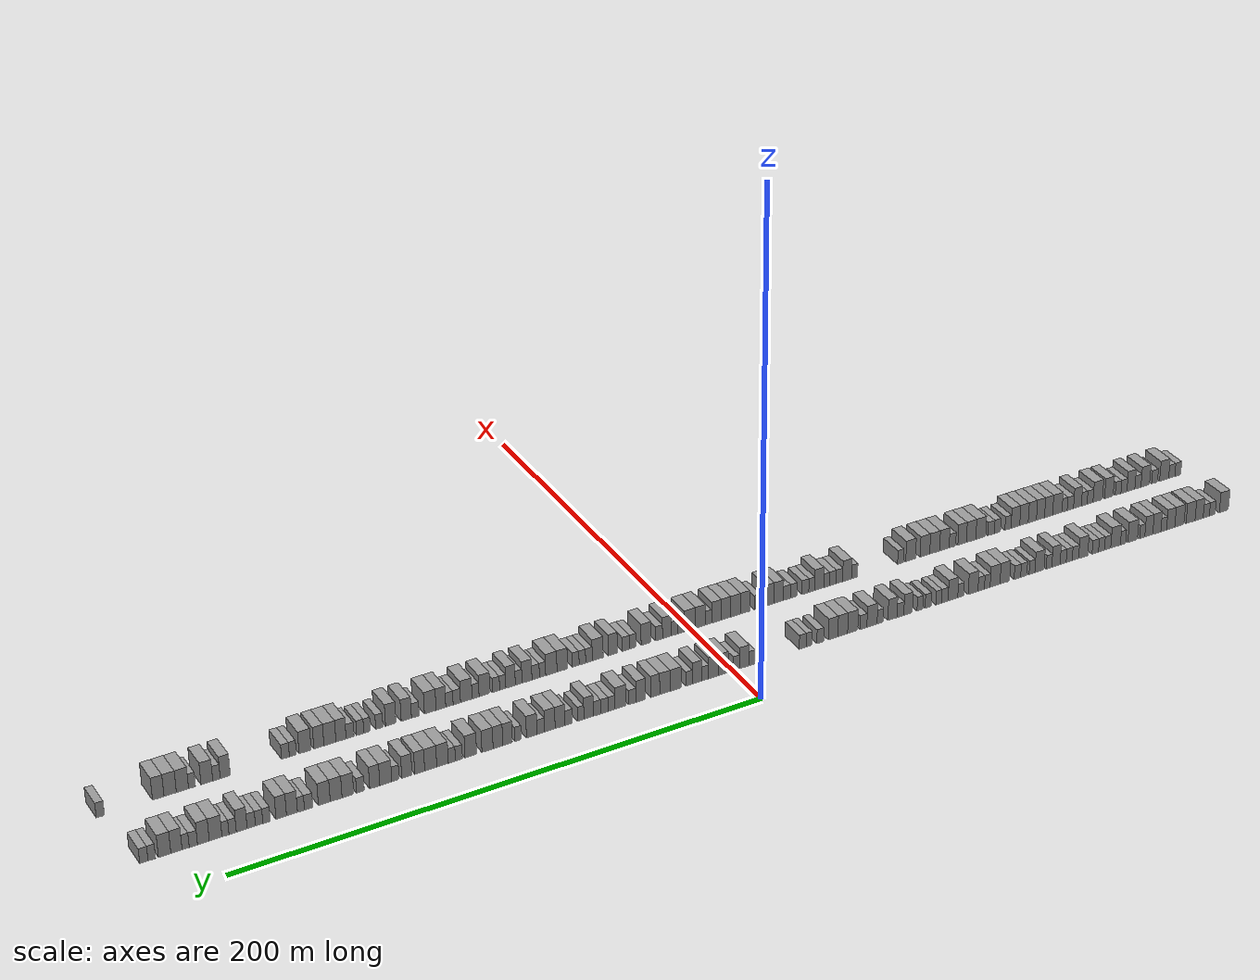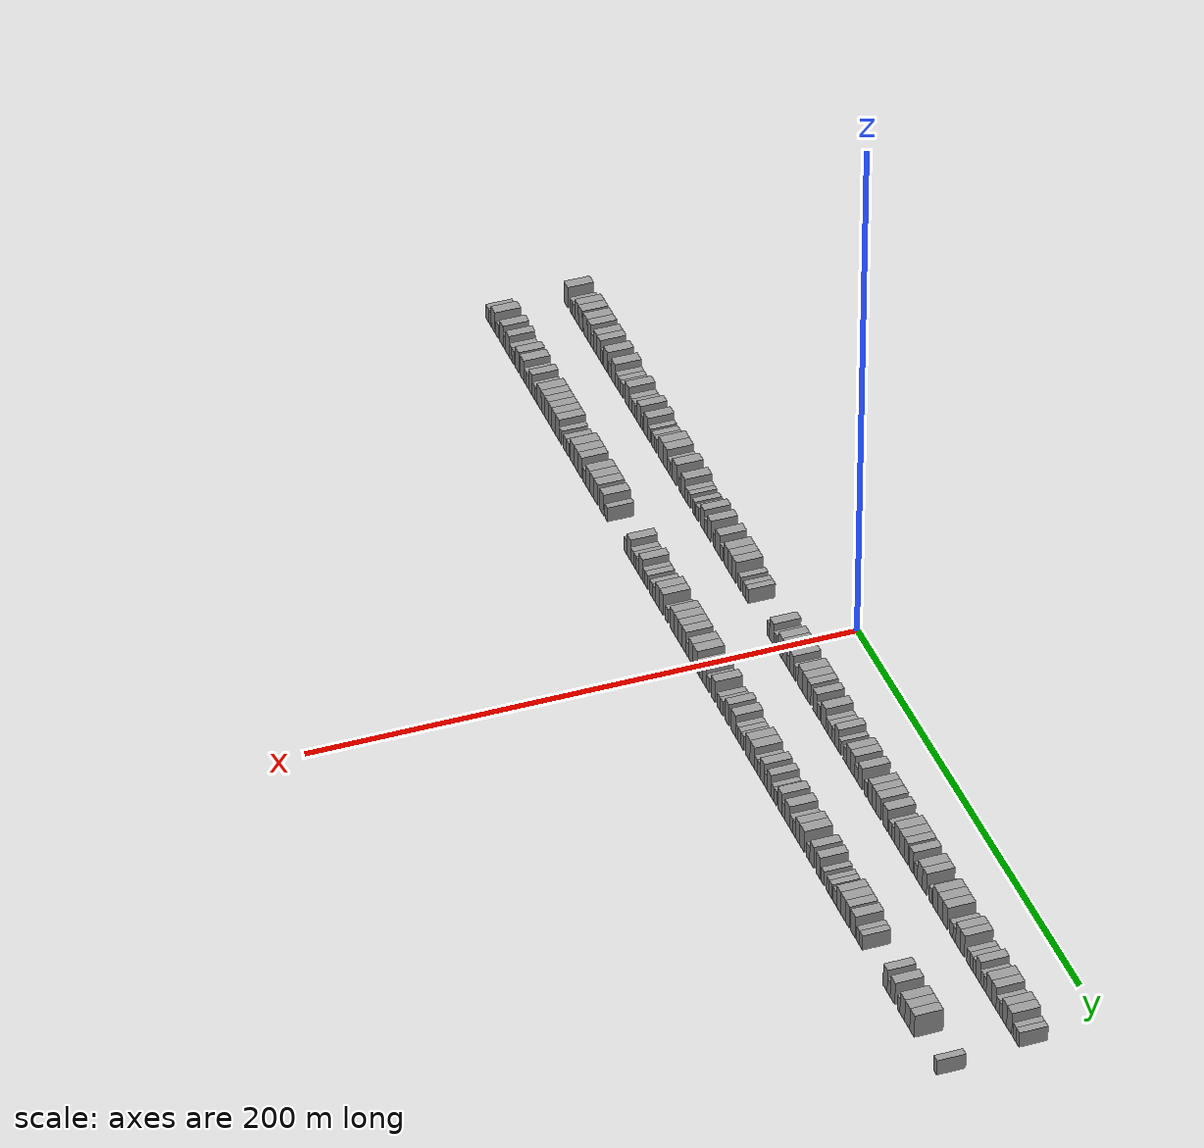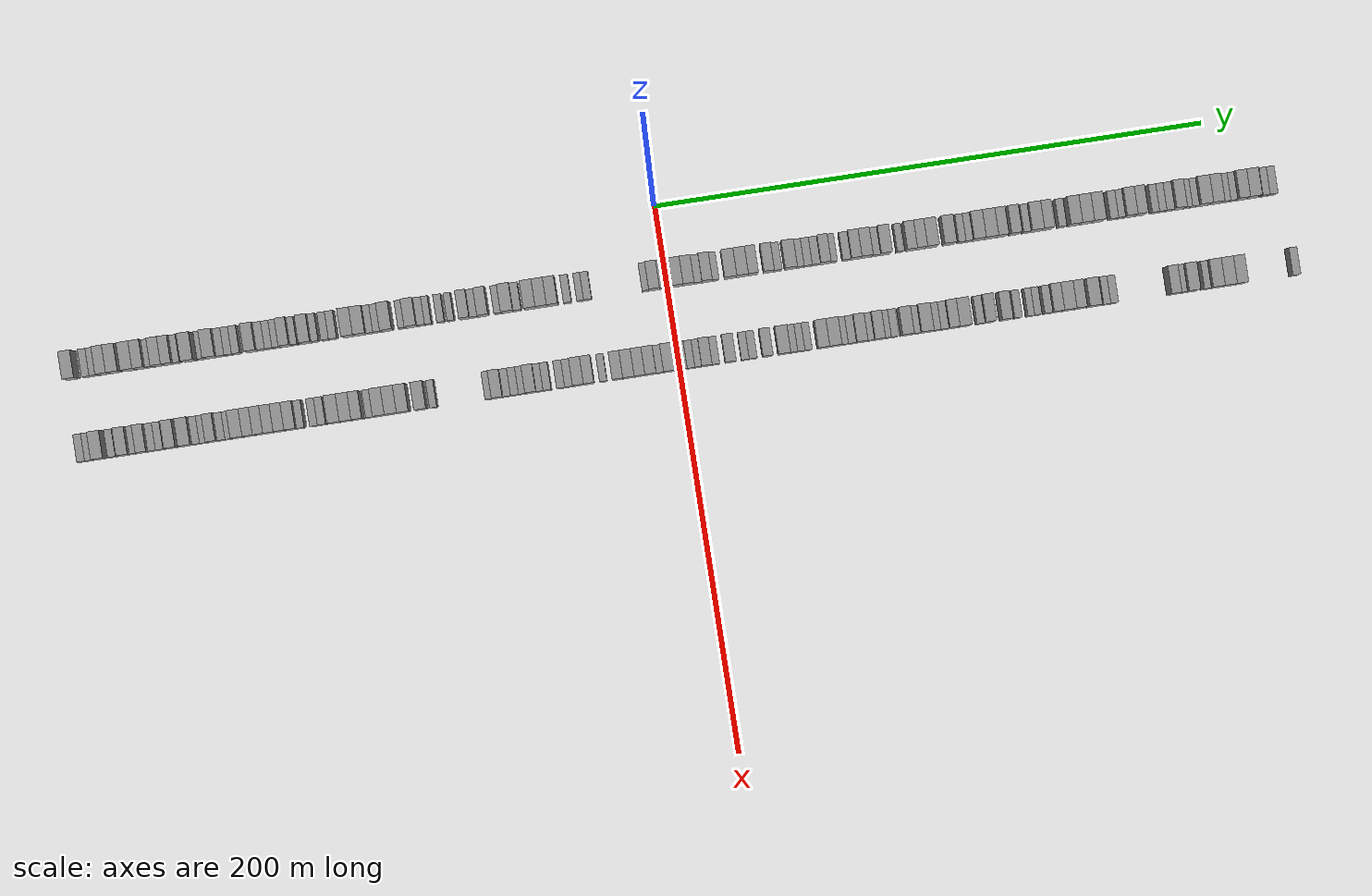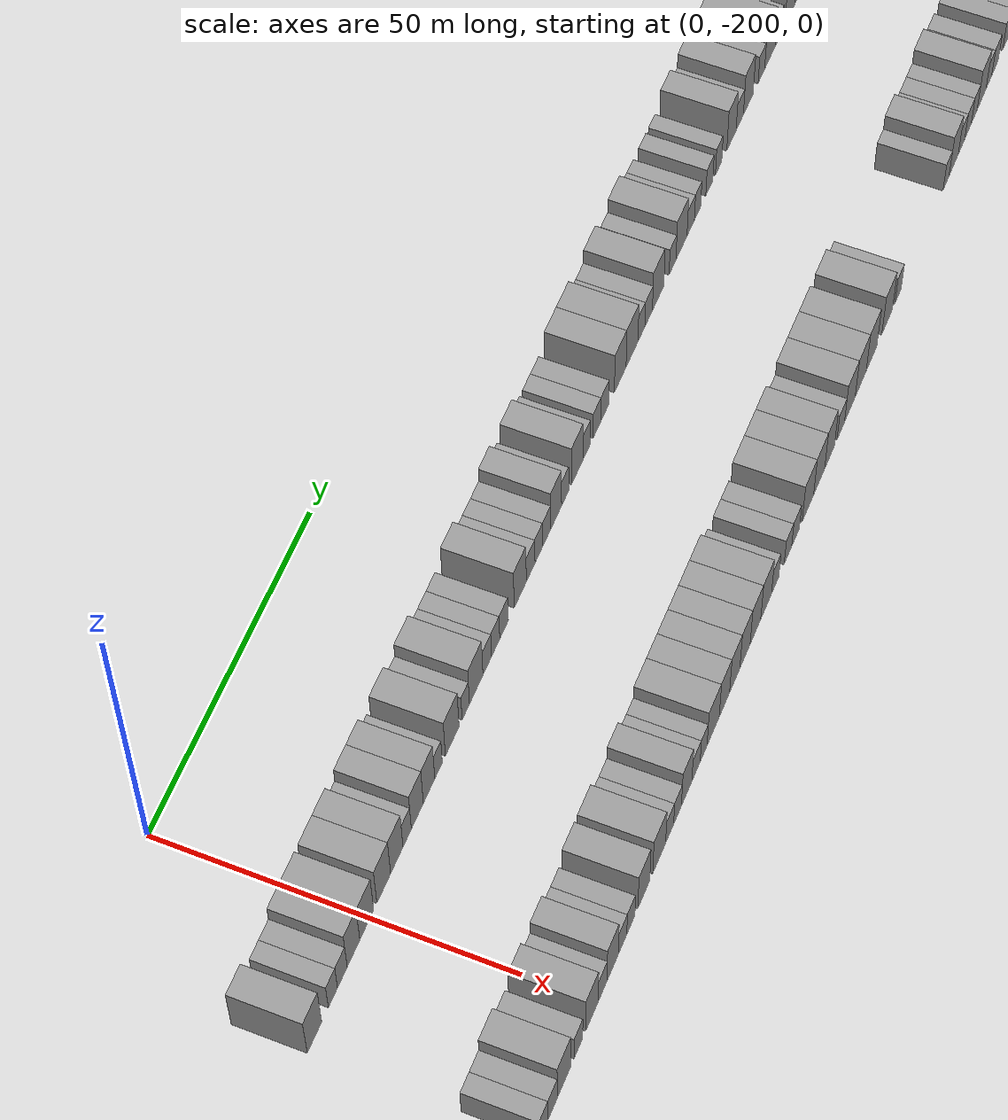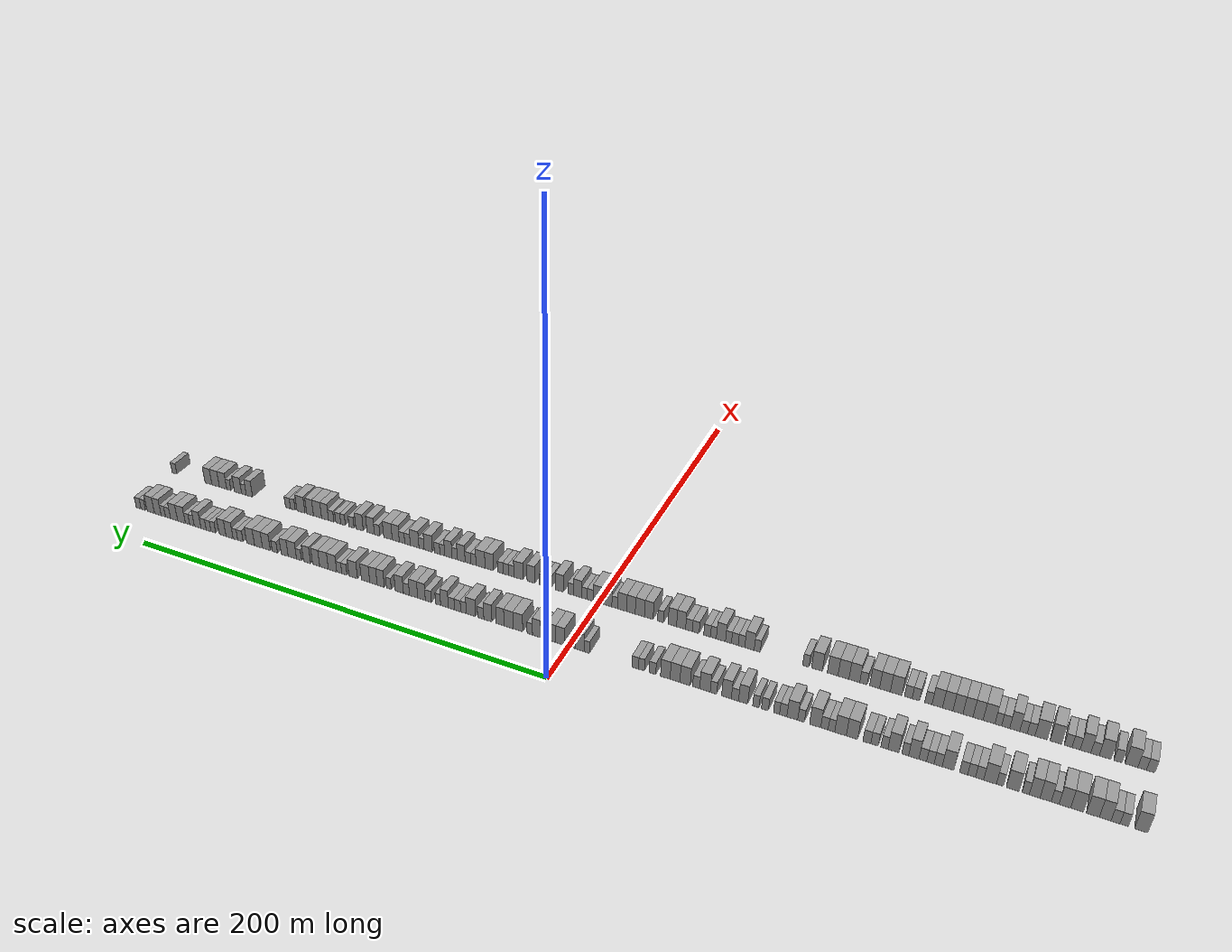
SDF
<sdf version="1.6">
 <world name="default">
  <scene>
   <sky><clouds><speed>12</speed></clouds></sky>
   <ambient>0.4 0.4 0.4 1</ambient>
   <background>0.7 0.7 0.7 1</background>
   <shadows>1</shadows>
  </scene>
  <gravity>0 0 -9.8066</gravity>
  <magnetic_field>6e-06 2.3e-05 -4.2e-05</magnetic_field>
  <physics default="0" name="default_physics" type="ode">
   <ode>
    <solver>
     <type>quick</type>
     <iters>10</iters>
     <sor>1.0</sor>
     <use_dynamic_moi_rescaling>0</use_dynamic_moi_rescaling>
    </solver>
    <constraints>
     <cfm>0</cfm>
     <erp>0.2</erp>
     <contact_max_correcting_vel>100</contact_max_correcting_vel>
     <contact_surface_layer>0.001</contact_surface_layer>
    </constraints>
   </ode>
   <max_step_size>0.004</max_step_size>
   <real_time_factor>1</real_time_factor>
   <real_time_update_rate>250</real_time_update_rate>
  </physics>
  <light name="sun" type="directional">
   <pose>0 0 10 0 0 0</pose>
   <diffuse>0.8 0.8 0.8 1</diffuse>
   <specular>0.2 0.2 0.2 1</specular>
   <attenuation>
    <range>1000</range>
    <constant>0.9</constant>
    <linear>0.01</linear>
    <quadratic>0.001</quadratic>
   </attenuation>
   <direction>-0.5 0.1 -0.9</direction>
  </light>
  <model name="building_1">
   <static>1</static>
   <pose>25.0000 -216.8449 0 0.000000 0.000000 0.000000</pose>
   <link name="link">
    <pose>0 0 4.50 0 0 0</pose>
    <collision name="collision"><geometry><box><size>10.0000 4.3102 9.0000</size></box></geometry></collision>
    <visual name="visual">
     <cast_shadows>0</cast_shadows>
     <geometry><box><size>10.0000 4.3102 9.0000</size></box></geometry>
     <material>
      <script>
       <uri>model://grey_wall/materials/scripts</uri>
       <uri>model://grey_wall/materials/textures</uri>
       <name>vrc/grey_wall</name>
      </script>
     </material>
    </visual>
   </link>
  </model>
  <model name="building_2">
   <static>1</static>
   <pose>25.0000 -211.3207 0 0.000000 0.000000 0.000000</pose>
   <link name="link">
    <pose>0 0 3.00 0 0 0</pose>
    <collision name="collision"><geometry><box><size>10.0000 2.7383 6.0000</size></box></geometry></collision>
    <visual name="visual">
     <cast_shadows>0</cast_shadows>
     <geometry><box><size>10.0000 2.7383 6.0000</size></box></geometry>
     <material>
      <script>
       <uri>model://grey_wall/materials/scripts</uri>
       <uri>model://grey_wall/materials/textures</uri>
       <name>vrc/grey_wall</name>
      </script>
     </material>
    </visual>
   </link>
  </model>
  <model name="building_3">
   <static>1</static>
   <pose>25.0000 -208.4802 0 0.000000 0.000000 0.000000</pose>
   <link name="link">
    <pose>0 0 3.00 0 0 0</pose>
    <collision name="collision"><geometry><box><size>10.0000 2.9428 6.0000</size></box></geometry></collision>
    <visual name="visual">
     <cast_shadows>0</cast_shadows>
     <geometry><box><size>10.0000 2.9428 6.0000</size></box></geometry>
     <material>
      <script>
       <uri>model://grey_wall/materials/scripts</uri>
       <uri>model://grey_wall/materials/textures</uri>
       <name>vrc/grey_wall</name>
      </script>
     </material>
    </visual>
   </link>
  </model>
  <model name="building_4">
   <static>1</static>
   <pose>25.0000 -205.0860 0 0.000000 0.000000 0.000000</pose>
   <link name="link">
    <pose>0 0 4.50 0 0 0</pose>
    <collision name="collision"><geometry><box><size>10.0000 3.8455 9.0000</size></box></geometry></collision>
    <visual name="visual">
     <cast_shadows>0</cast_shadows>
     <geometry><box><size>10.0000 3.8455 9.0000</size></box></geometry>
     <material>
      <script>
       <uri>model://grey_wall/materials/scripts</uri>
       <uri>model://grey_wall/materials/textures</uri>
       <name>vrc/grey_wall</name>
      </script>
     </material>
    </visual>
   </link>
  </model>
  <model name="building_5">
   <static>1</static>
   <pose>25.0000 -201.0312 0 0.000000 0.000000 0.000000</pose>
   <link name="link">
    <pose>0 0 4.50 0 0 0</pose>
    <collision name="collision"><geometry><box><size>10.0000 4.2641 9.0000</size></box></geometry></collision>
    <visual name="visual">
     <cast_shadows>0</cast_shadows>
     <geometry><box><size>10.0000 4.2641 9.0000</size></box></geometry>
     <material>
      <script>
       <uri>model://grey_wall/materials/scripts</uri>
       <uri>model://grey_wall/materials/textures</uri>
       <name>vrc/grey_wall</name>
      </script>
     </material>
    </visual>
   </link>
  </model>
  <model name="building_6">
   <static>1</static>
   <pose>25.0000 -195.7568 0 0.000000 0.000000 0.000000</pose>
   <link name="link">
    <pose>0 0 4.50 0 0 0</pose>
    <collision name="collision"><geometry><box><size>10.0000 4.2846 9.0000</size></box></geometry></collision>
    <visual name="visual">
     <cast_shadows>0</cast_shadows>
     <geometry><box><size>10.0000 4.2846 9.0000</size></box></geometry>
     <material>
      <script>
       <uri>model://grey_wall/materials/scripts</uri>
       <uri>model://grey_wall/materials/textures</uri>
       <name>vrc/grey_wall</name>
      </script>
     </material>
    </visual>
   </link>
  </model>
  <model name="building_7">
   <static>1</static>
   <pose>25.0000 -191.6710 0 0.000000 0.000000 0.000000</pose>
   <link name="link">
    <pose>0 0 4.50 0 0 0</pose>
    <collision name="collision"><geometry><box><size>10.0000 3.8869 9.0000</size></box></geometry></collision>
    <visual name="visual">
     <cast_shadows>0</cast_shadows>
     <geometry><box><size>10.0000 3.8869 9.0000</size></box></geometry>
     <material>
      <script>
       <uri>model://grey_wall/materials/scripts</uri>
       <uri>model://grey_wall/materials/textures</uri>
       <name>vrc/grey_wall</name>
      </script>
     </material>
    </visual>
   </link>
  </model>
  <model name="building_8">
   <static>1</static>
   <pose>25.0000 -188.4047 0 0.000000 0.000000 0.000000</pose>
   <link name="link">
    <pose>0 0 3.00 0 0 0</pose>
    <collision name="collision"><geometry><box><size>10.0000 2.6456 6.0000</size></box></geometry></collision>
    <visual name="visual">
     <cast_shadows>0</cast_shadows>
     <geometry><box><size>10.0000 2.6456 6.0000</size></box></geometry>
     <material>
      <script>
       <uri>model://grey_wall/materials/scripts</uri>
       <uri>model://grey_wall/materials/textures</uri>
       <name>vrc/grey_wall</name>
      </script>
     </material>
    </visual>
   </link>
  </model>
  <model name="building_9">
   <static>1</static>
   <pose>25.0000 -185.1813 0 0.000000 0.000000 0.000000</pose>
   <link name="link">
    <pose>0 0 4.50 0 0 0</pose>
    <collision name="collision"><geometry><box><size>10.0000 3.8012 9.0000</size></box></geometry></collision>
    <visual name="visual">
     <cast_shadows>0</cast_shadows>
     <geometry><box><size>10.0000 3.8012 9.0000</size></box></geometry>
     <material>
      <script>
       <uri>model://grey_wall/materials/scripts</uri>
       <uri>model://grey_wall/materials/textures</uri>
       <name>vrc/grey_wall</name>
      </script>
     </material>
    </visual>
   </link>
  </model>
  <model name="building_10">
   <static>1</static>
   <pose>25.0000 -181.4406 0 0.000000 0.000000 0.000000</pose>
   <link name="link">
    <pose>0 0 4.50 0 0 0</pose>
    <collision name="collision"><geometry><box><size>10.0000 3.6803 9.0000</size></box></geometry></collision>
    <visual name="visual">
     <cast_shadows>0</cast_shadows>
     <geometry><box><size>10.0000 3.6803 9.0000</size></box></geometry>
     <material>
      <script>
       <uri>model://grey_wall/materials/scripts</uri>
       <uri>model://grey_wall/materials/textures</uri>
       <name>vrc/grey_wall</name>
      </script>
     </material>
    </visual>
   </link>
  </model>
  <model name="building_11">
   <static>1</static>
   <pose>25.0000 -178.3902 0 0.000000 0.000000 0.000000</pose>
   <link name="link">
    <pose>0 0 3.00 0 0 0</pose>
    <collision name="collision"><geometry><box><size>10.0000 2.4205 6.0000</size></box></geometry></collision>
    <visual name="visual">
     <cast_shadows>0</cast_shadows>
     <geometry><box><size>10.0000 2.4205 6.0000</size></box></geometry>
     <material>
      <script>
       <uri>model://grey_wall/materials/scripts</uri>
       <uri>model://grey_wall/materials/textures</uri>
       <name>vrc/grey_wall</name>
      </script>
     </material>
    </visual>
   </link>
  </model>
  <model name="building_12">
   <static>1</static>
   <pose>25.0000 -173.9507 0 0.000000 0.000000 0.000000</pose>
   <link name="link">
    <pose>0 0 4.50 0 0 0</pose>
    <collision name="collision"><geometry><box><size>10.0000 4.4586 9.0000</size></box></geometry></collision>
    <visual name="visual">
     <cast_shadows>0</cast_shadows>
     <geometry><box><size>10.0000 4.4586 9.0000</size></box></geometry>
     <material>
      <script>
       <uri>model://grey_wall/materials/scripts</uri>
       <uri>model://grey_wall/materials/textures</uri>
       <name>vrc/grey_wall</name>
      </script>
     </material>
    </visual>
   </link>
  </model>
  <model name="building_13">
   <static>1</static>
   <pose>25.0000 -169.5160 0 0.000000 0.000000 0.000000</pose>
   <link name="link">
    <pose>0 0 3.00 0 0 0</pose>
    <collision name="collision"><geometry><box><size>10.0000 2.4110 6.0000</size></box></geometry></collision>
    <visual name="visual">
     <cast_shadows>0</cast_shadows>
     <geometry><box><size>10.0000 2.4110 6.0000</size></box></geometry>
     <material>
      <script>
       <uri>model://grey_wall/materials/scripts</uri>
       <uri>model://grey_wall/materials/textures</uri>
       <name>vrc/grey_wall</name>
      </script>
     </material>
    </visual>
   </link>
  </model>
  <model name="building_14">
   <static>1</static>
   <pose>25.0000 -166.0705 0 0.000000 0.000000 0.000000</pose>
   <link name="link">
    <pose>0 0 4.50 0 0 0</pose>
    <collision name="collision"><geometry><box><size>10.0000 4.4799 9.0000</size></box></geometry></collision>
    <visual name="visual">
     <cast_shadows>0</cast_shadows>
     <geometry><box><size>10.0000 4.4799 9.0000</size></box></geometry>
     <material>
      <script>
       <uri>model://grey_wall/materials/scripts</uri>
       <uri>model://grey_wall/materials/textures</uri>
       <name>vrc/grey_wall</name>
      </script>
     </material>
    </visual>
   </link>
  </model>
  <model name="building_15">
   <static>1</static>
   <pose>25.0000 -162.4017 0 0.000000 0.000000 0.000000</pose>
   <link name="link">
    <pose>0 0 3.00 0 0 0</pose>
    <collision name="collision"><geometry><box><size>10.0000 2.8579 6.0000</size></box></geometry></collision>
    <visual name="visual">
     <cast_shadows>0</cast_shadows>
     <geometry><box><size>10.0000 2.8579 6.0000</size></box></geometry>
     <material>
      <script>
       <uri>model://grey_wall/materials/scripts</uri>
       <uri>model://grey_wall/materials/textures</uri>
       <name>vrc/grey_wall</name>
      </script>
     </material>
    </visual>
   </link>
  </model>
  <model name="building_16">
   <static>1</static>
   <pose>25.0000 -159.5947 0 0.000000 0.000000 0.000000</pose>
   <link name="link">
    <pose>0 0 3.00 0 0 0</pose>
    <collision name="collision"><geometry><box><size>10.0000 2.7561 6.0000</size></box></geometry></collision>
    <visual name="visual">
     <cast_shadows>0</cast_shadows>
     <geometry><box><size>10.0000 2.7561 6.0000</size></box></geometry>
     <material>
      <script>
       <uri>model://grey_wall/materials/scripts</uri>
       <uri>model://grey_wall/materials/textures</uri>
       <name>vrc/grey_wall</name>
      </script>
     </material>
    </visual>
   </link>
  </model>
  <model name="building_17">
   <static>1</static>
   <pose>25.0000 -156.7591 0 0.000000 0.000000 0.000000</pose>
   <link name="link">
    <pose>0 0 3.00 0 0 0</pose>
    <collision name="collision"><geometry><box><size>10.0000 2.9151 6.0000</size></box></geometry></collision>
    <visual name="visual">
     <cast_shadows>0</cast_shadows>
     <geometry><box><size>10.0000 2.9151 6.0000</size></box></geometry>
     <material>
      <script>
       <uri>model://grey_wall/materials/scripts</uri>
       <uri>model://grey_wall/materials/textures</uri>
       <name>vrc/grey_wall</name>
      </script>
     </material>
    </visual>
   </link>
  </model>
  <model name="building_18">
   <static>1</static>
   <pose>25.0000 -151.2368 0 0.000000 0.000000 0.000000</pose>
   <link name="link">
    <pose>0 0 4.50 0 0 0</pose>
    <collision name="collision"><geometry><box><size>10.0000 4.1294 9.0000</size></box></geometry></collision>
    <visual name="visual">
     <cast_shadows>0</cast_shadows>
     <geometry><box><size>10.0000 4.1294 9.0000</size></box></geometry>
     <material>
      <script>
       <uri>model://grey_wall/materials/scripts</uri>
       <uri>model://grey_wall/materials/textures</uri>
       <name>vrc/grey_wall</name>
      </script>
     </material>
    </visual>
   </link>
  </model>
  <model name="building_19">
   <static>1</static>
   <pose>25.0000 -147.6917 0 0.000000 0.000000 0.000000</pose>
   <link name="link">
    <pose>0 0 3.00 0 0 0</pose>
    <collision name="collision"><geometry><box><size>10.0000 2.9608 6.0000</size></box></geometry></collision>
    <visual name="visual">
     <cast_shadows>0</cast_shadows>
     <geometry><box><size>10.0000 2.9608 6.0000</size></box></geometry>
     <material>
      <script>
       <uri>model://grey_wall/materials/scripts</uri>
       <uri>model://grey_wall/materials/textures</uri>
       <name>vrc/grey_wall</name>
      </script>
     </material>
    </visual>
   </link>
  </model>
  <model name="building_20">
   <static>1</static>
   <pose>25.0000 -144.8623 0 0.000000 0.000000 0.000000</pose>
   <link name="link">
    <pose>0 0 3.00 0 0 0</pose>
    <collision name="collision"><geometry><box><size>10.0000 2.6980 6.0000</size></box></geometry></collision>
    <visual name="visual">
     <cast_shadows>0</cast_shadows>
     <geometry><box><size>10.0000 2.6980 6.0000</size></box></geometry>
     <material>
      <script>
       <uri>model://grey_wall/materials/scripts</uri>
       <uri>model://grey_wall/materials/textures</uri>
       <name>vrc/grey_wall</name>
      </script>
     </material>
    </visual>
   </link>
  </model>
  <model name="building_21">
   <static>1</static>
   <pose>25.0000 -142.1148 0 0.000000 0.000000 0.000000</pose>
   <link name="link">
    <pose>0 0 3.00 0 0 0</pose>
    <collision name="collision"><geometry><box><size>10.0000 2.7970 6.0000</size></box></geometry></collision>
    <visual name="visual">
     <cast_shadows>0</cast_shadows>
     <geometry><box><size>10.0000 2.7970 6.0000</size></box></geometry>
     <material>
      <script>
       <uri>model://grey_wall/materials/scripts</uri>
       <uri>model://grey_wall/materials/textures</uri>
       <name>vrc/grey_wall</name>
      </script>
     </material>
    </visual>
   </link>
  </model>
  <model name="building_22">
   <static>1</static>
   <pose>25.0000 -138.8480 0 0.000000 0.000000 0.000000</pose>
   <link name="link">
    <pose>0 0 4.50 0 0 0</pose>
    <collision name="collision"><geometry><box><size>10.0000 3.7365 9.0000</size></box></geometry></collision>
    <visual name="visual">
     <cast_shadows>0</cast_shadows>
     <geometry><box><size>10.0000 3.7365 9.0000</size></box></geometry>
     <material>
      <script>
       <uri>model://grey_wall/materials/scripts</uri>
       <uri>model://grey_wall/materials/textures</uri>
       <name>vrc/grey_wall</name>
      </script>
     </material>
    </visual>
   </link>
  </model>
  <model name="building_23">
   <static>1</static>
   <pose>25.0000 -135.7185 0 0.000000 0.000000 0.000000</pose>
   <link name="link">
    <pose>0 0 3.00 0 0 0</pose>
    <collision name="collision"><geometry><box><size>10.0000 2.5227 6.0000</size></box></geometry></collision>
    <visual name="visual">
     <cast_shadows>0</cast_shadows>
     <geometry><box><size>10.0000 2.5227 6.0000</size></box></geometry>
     <material>
      <script>
       <uri>model://grey_wall/materials/scripts</uri>
       <uri>model://grey_wall/materials/textures</uri>
       <name>vrc/grey_wall</name>
      </script>
     </material>
    </visual>
   </link>
  </model>
  <model name="building_24">
   <static>1</static>
   <pose>25.0000 -131.4101 0 0.000000 0.000000 0.000000</pose>
   <link name="link">
    <pose>0 0 4.50 0 0 0</pose>
    <collision name="collision"><geometry><box><size>10.0000 4.0940 9.0000</size></box></geometry></collision>
    <visual name="visual">
     <cast_shadows>0</cast_shadows>
     <geometry><box><size>10.0000 4.0940 9.0000</size></box></geometry>
     <material>
      <script>
       <uri>model://grey_wall/materials/scripts</uri>
       <uri>model://grey_wall/materials/textures</uri>
       <name>vrc/grey_wall</name>
      </script>
     </material>
    </visual>
   </link>
  </model>
  <model name="building_25">
   <static>1</static>
   <pose>25.0000 -128.0672 0 0.000000 0.000000 0.000000</pose>
   <link name="link">
    <pose>0 0 3.00 0 0 0</pose>
    <collision name="collision"><geometry><box><size>10.0000 2.5918 6.0000</size></box></geometry></collision>
    <visual name="visual">
     <cast_shadows>0</cast_shadows>
     <geometry><box><size>10.0000 2.5918 6.0000</size></box></geometry>
     <material>
      <script>
       <uri>model://grey_wall/materials/scripts</uri>
       <uri>model://grey_wall/materials/textures</uri>
       <name>vrc/grey_wall</name>
      </script>
     </material>
    </visual>
   </link>
  </model>
  <model name="building_26">
   <static>1</static>
   <pose>25.0000 -124.3897 0 0.000000 0.000000 0.000000</pose>
   <link name="link">
    <pose>0 0 3.00 0 0 0</pose>
    <collision name="collision"><geometry><box><size>10.0000 2.7630 6.0000</size></box></geometry></collision>
    <visual name="visual">
     <cast_shadows>0</cast_shadows>
     <geometry><box><size>10.0000 2.7630 6.0000</size></box></geometry>
     <material>
      <script>
       <uri>model://grey_wall/materials/scripts</uri>
       <uri>model://grey_wall/materials/textures</uri>
       <name>vrc/grey_wall</name>
      </script>
     </material>
    </visual>
   </link>
  </model>
  <model name="building_27">
   <static>1</static>
   <pose>25.0000 -121.5438 0 0.000000 0.000000 0.000000</pose>
   <link name="link">
    <pose>0 0 3.00 0 0 0</pose>
    <collision name="collision"><geometry><box><size>10.0000 2.9288 6.0000</size></box></geometry></collision>
    <visual name="visual">
     <cast_shadows>0</cast_shadows>
     <geometry><box><size>10.0000 2.9288 6.0000</size></box></geometry>
     <material>
      <script>
       <uri>model://grey_wall/materials/scripts</uri>
       <uri>model://grey_wall/materials/textures</uri>
       <name>vrc/grey_wall</name>
      </script>
     </material>
    </visual>
   </link>
  </model>
  <model name="building_28">
   <static>1</static>
   <pose>25.0000 -115.9444 0 0.000000 0.000000 0.000000</pose>
   <link name="link">
    <pose>0 0 4.50 0 0 0</pose>
    <collision name="collision"><geometry><box><size>10.0000 4.2701 9.0000</size></box></geometry></collision>
    <visual name="visual">
     <cast_shadows>0</cast_shadows>
     <geometry><box><size>10.0000 4.2701 9.0000</size></box></geometry>
     <material>
      <script>
       <uri>model://grey_wall/materials/scripts</uri>
       <uri>model://grey_wall/materials/textures</uri>
       <name>vrc/grey_wall</name>
      </script>
     </material>
    </visual>
   </link>
  </model>
  <model name="building_29">
   <static>1</static>
   <pose>25.0000 -111.6163 0 0.000000 0.000000 0.000000</pose>
   <link name="link">
    <pose>0 0 4.50 0 0 0</pose>
    <collision name="collision"><geometry><box><size>10.0000 4.3861 9.0000</size></box></geometry></collision>
    <visual name="visual">
     <cast_shadows>0</cast_shadows>
     <geometry><box><size>10.0000 4.3861 9.0000</size></box></geometry>
     <material>
      <script>
       <uri>model://grey_wall/materials/scripts</uri>
       <uri>model://grey_wall/materials/textures</uri>
       <name>vrc/grey_wall</name>
      </script>
     </material>
    </visual>
   </link>
  </model>
  <model name="building_30">
   <static>1</static>
   <pose>25.0000 -108.1566 0 0.000000 0.000000 0.000000</pose>
   <link name="link">
    <pose>0 0 3.00 0 0 0</pose>
    <collision name="collision"><geometry><box><size>10.0000 2.5332 6.0000</size></box></geometry></collision>
    <visual name="visual">
     <cast_shadows>0</cast_shadows>
     <geometry><box><size>10.0000 2.5332 6.0000</size></box></geometry>
     <material>
      <script>
       <uri>model://grey_wall/materials/scripts</uri>
       <uri>model://grey_wall/materials/textures</uri>
       <name>vrc/grey_wall</name>
      </script>
     </material>
    </visual>
   </link>
  </model>
  <model name="building_31">
   <static>1</static>
   <pose>25.0000 -105.4735 0 0.000000 0.000000 0.000000</pose>
   <link name="link">
    <pose>0 0 3.00 0 0 0</pose>
    <collision name="collision"><geometry><box><size>10.0000 2.8330 6.0000</size></box></geometry></collision>
    <visual name="visual">
     <cast_shadows>0</cast_shadows>
     <geometry><box><size>10.0000 2.8330 6.0000</size></box></geometry>
     <material>
      <script>
       <uri>model://grey_wall/materials/scripts</uri>
       <uri>model://grey_wall/materials/textures</uri>
       <name>vrc/grey_wall</name>
      </script>
     </material>
    </visual>
   </link>
  </model>
  <model name="building_32">
   <static>1</static>
   <pose>25.0000 -101.9138 0 0.000000 0.000000 0.000000</pose>
   <link name="link">
    <pose>0 0 4.50 0 0 0</pose>
    <collision name="collision"><geometry><box><size>10.0000 4.2863 9.0000</size></box></geometry></collision>
    <visual name="visual">
     <cast_shadows>0</cast_shadows>
     <geometry><box><size>10.0000 4.2863 9.0000</size></box></geometry>
     <material>
      <script>
       <uri>model://grey_wall/materials/scripts</uri>
       <uri>model://grey_wall/materials/textures</uri>
       <name>vrc/grey_wall</name>
      </script>
     </material>
    </visual>
   </link>
  </model>
  <model name="building_33">
   <static>1</static>
   <pose>25.0000 -96.4714 0 0.000000 0.000000 0.000000</pose>
   <link name="link">
    <pose>0 0 3.00 0 0 0</pose>
    <collision name="collision"><geometry><box><size>10.0000 2.5985 6.0000</size></box></geometry></collision>
    <visual name="visual">
     <cast_shadows>0</cast_shadows>
     <geometry><box><size>10.0000 2.5985 6.0000</size></box></geometry>
     <material>
      <script>
       <uri>model://grey_wall/materials/scripts</uri>
       <uri>model://grey_wall/materials/textures</uri>
       <name>vrc/grey_wall</name>
      </script>
     </material>
    </visual>
   </link>
  </model>
  <model name="building_34">
   <static>1</static>
   <pose>25.0000 -93.0581 0 0.000000 0.000000 0.000000</pose>
   <link name="link">
    <pose>0 0 4.50 0 0 0</pose>
    <collision name="collision"><geometry><box><size>10.0000 4.2281 9.0000</size></box></geometry></collision>
    <visual name="visual">
     <cast_shadows>0</cast_shadows>
     <geometry><box><size>10.0000 4.2281 9.0000</size></box></geometry>
     <material>
      <script>
       <uri>model://grey_wall/materials/scripts</uri>
       <uri>model://grey_wall/materials/textures</uri>
       <name>vrc/grey_wall</name>
      </script>
     </material>
    </visual>
   </link>
  </model>
  <model name="building_35">
   <static>1</static>
   <pose>25.0000 -89.5217 0 0.000000 0.000000 0.000000</pose>
   <link name="link">
    <pose>0 0 3.00 0 0 0</pose>
    <collision name="collision"><geometry><box><size>10.0000 2.8448 6.0000</size></box></geometry></collision>
    <visual name="visual">
     <cast_shadows>0</cast_shadows>
     <geometry><box><size>10.0000 2.8448 6.0000</size></box></geometry>
     <material>
      <script>
       <uri>model://grey_wall/materials/scripts</uri>
       <uri>model://grey_wall/materials/textures</uri>
       <name>vrc/grey_wall</name>
      </script>
     </material>
    </visual>
   </link>
  </model>
  <model name="building_36">
   <static>1</static>
   <pose>25.0000 -86.8919 0 0.000000 0.000000 0.000000</pose>
   <link name="link">
    <pose>0 0 3.00 0 0 0</pose>
    <collision name="collision"><geometry><box><size>10.0000 2.4148 6.0000</size></box></geometry></collision>
    <visual name="visual">
     <cast_shadows>0</cast_shadows>
     <geometry><box><size>10.0000 2.4148 6.0000</size></box></geometry>
     <material>
      <script>
       <uri>model://grey_wall/materials/scripts</uri>
       <uri>model://grey_wall/materials/textures</uri>
       <name>vrc/grey_wall</name>
      </script>
     </material>
    </visual>
   </link>
  </model>
  <model name="building_37">
   <static>1</static>
   <pose>25.0000 -82.3169 0 0.000000 0.000000 0.000000</pose>
   <link name="link">
    <pose>0 0 3.00 0 0 0</pose>
    <collision name="collision"><geometry><box><size>10.0000 2.7351 6.0000</size></box></geometry></collision>
    <visual name="visual">
     <cast_shadows>0</cast_shadows>
     <geometry><box><size>10.0000 2.7351 6.0000</size></box></geometry>
     <material>
      <script>
       <uri>model://grey_wall/materials/scripts</uri>
       <uri>model://grey_wall/materials/textures</uri>
       <name>vrc/grey_wall</name>
      </script>
     </material>
    </visual>
   </link>
  </model>
  <model name="building_38">
   <static>1</static>
   <pose>25.0000 -78.6994 0 0.000000 0.000000 0.000000</pose>
   <link name="link">
    <pose>0 0 3.00 0 0 0</pose>
    <collision name="collision"><geometry><box><size>10.0000 2.4998 6.0000</size></box></geometry></collision>
    <visual name="visual">
     <cast_shadows>0</cast_shadows>
     <geometry><box><size>10.0000 2.4998 6.0000</size></box></geometry>
     <material>
      <script>
       <uri>model://grey_wall/materials/scripts</uri>
       <uri>model://grey_wall/materials/textures</uri>
       <name>vrc/grey_wall</name>
      </script>
     </material>
    </visual>
   </link>
  </model>
  <model name="building_39">
   <static>1</static>
   <pose>25.0000 -73.6021 0 0.000000 0.000000 0.000000</pose>
   <link name="link">
    <pose>0 0 4.50 0 0 0</pose>
    <collision name="collision"><geometry><box><size>10.0000 3.6949 9.0000</size></box></geometry></collision>
    <visual name="visual">
     <cast_shadows>0</cast_shadows>
     <geometry><box><size>10.0000 3.6949 9.0000</size></box></geometry>
     <material>
      <script>
       <uri>model://grey_wall/materials/scripts</uri>
       <uri>model://grey_wall/materials/textures</uri>
       <name>vrc/grey_wall</name>
      </script>
     </material>
    </visual>
   </link>
  </model>
  <model name="building_40">
   <static>1</static>
   <pose>25.0000 -70.3064 0 0.000000 0.000000 0.000000</pose>
   <link name="link">
    <pose>0 0 3.00 0 0 0</pose>
    <collision name="collision"><geometry><box><size>10.0000 2.8964 6.0000</size></box></geometry></collision>
    <visual name="visual">
     <cast_shadows>0</cast_shadows>
     <geometry><box><size>10.0000 2.8964 6.0000</size></box></geometry>
     <material>
      <script>
       <uri>model://grey_wall/materials/scripts</uri>
       <uri>model://grey_wall/materials/textures</uri>
       <name>vrc/grey_wall</name>
      </script>
     </material>
    </visual>
   </link>
  </model>
  <model name="building_41">
   <static>1</static>
   <pose>25.0000 -66.8983 0 0.000000 0.000000 0.000000</pose>
   <link name="link">
    <pose>0 0 4.50 0 0 0</pose>
    <collision name="collision"><geometry><box><size>10.0000 3.9198 9.0000</size></box></geometry></collision>
    <visual name="visual">
     <cast_shadows>0</cast_shadows>
     <geometry><box><size>10.0000 3.9198 9.0000</size></box></geometry>
     <material>
      <script>
       <uri>model://grey_wall/materials/scripts</uri>
       <uri>model://grey_wall/materials/textures</uri>
       <name>vrc/grey_wall</name>
      </script>
     </material>
    </visual>
   </link>
  </model>
  <model name="building_42">
   <static>1</static>
   <pose>25.0000 -61.6221 0 0.000000 0.000000 0.000000</pose>
   <link name="link">
    <pose>0 0 3.00 0 0 0</pose>
    <collision name="collision"><geometry><box><size>10.0000 2.6326 6.0000</size></box></geometry></collision>
    <visual name="visual">
     <cast_shadows>0</cast_shadows>
     <geometry><box><size>10.0000 2.6326 6.0000</size></box></geometry>
     <material>
      <script>
       <uri>model://grey_wall/materials/scripts</uri>
       <uri>model://grey_wall/materials/textures</uri>
       <name>vrc/grey_wall</name>
      </script>
     </material>
    </visual>
   </link>
  </model>
  <model name="building_43">
   <static>1</static>
   <pose>25.0000 -58.1320 0 0.000000 0.000000 0.000000</pose>
   <link name="link">
    <pose>0 0 4.50 0 0 0</pose>
    <collision name="collision"><geometry><box><size>10.0000 4.3477 9.0000</size></box></geometry></collision>
    <visual name="visual">
     <cast_shadows>0</cast_shadows>
     <geometry><box><size>10.0000 4.3477 9.0000</size></box></geometry>
     <material>
      <script>
       <uri>model://grey_wall/materials/scripts</uri>
       <uri>model://grey_wall/materials/textures</uri>
       <name>vrc/grey_wall</name>
      </script>
     </material>
    </visual>
   </link>
  </model>
  <model name="building_44">
   <static>1</static>
   <pose>25.0000 -54.5126 0 0.000000 0.000000 0.000000</pose>
   <link name="link">
    <pose>0 0 3.00 0 0 0</pose>
    <collision name="collision"><geometry><box><size>10.0000 2.8912 6.0000</size></box></geometry></collision>
    <visual name="visual">
     <cast_shadows>0</cast_shadows>
     <geometry><box><size>10.0000 2.8912 6.0000</size></box></geometry>
     <material>
      <script>
       <uri>model://grey_wall/materials/scripts</uri>
       <uri>model://grey_wall/materials/textures</uri>
       <name>vrc/grey_wall</name>
      </script>
     </material>
    </visual>
   </link>
  </model>
  <model name="building_45">
   <static>1</static>
   <pose>25.0000 -49.9171 0 0.000000 0.000000 0.000000</pose>
   <link name="link">
    <pose>0 0 4.50 0 0 0</pose>
    <collision name="collision"><geometry><box><size>10.0000 4.2998 9.0000</size></box></geometry></collision>
    <visual name="visual">
     <cast_shadows>0</cast_shadows>
     <geometry><box><size>10.0000 4.2998 9.0000</size></box></geometry>
     <material>
      <script>
       <uri>model://grey_wall/materials/scripts</uri>
       <uri>model://grey_wall/materials/textures</uri>
       <name>vrc/grey_wall</name>
      </script>
     </material>
    </visual>
   </link>
  </model>
  <model name="building_46">
   <static>1</static>
   <pose>25.0000 -45.7218 0 0.000000 0.000000 0.000000</pose>
   <link name="link">
    <pose>0 0 4.50 0 0 0</pose>
    <collision name="collision"><geometry><box><size>10.0000 4.0908 9.0000</size></box></geometry></collision>
    <visual name="visual">
     <cast_shadows>0</cast_shadows>
     <geometry><box><size>10.0000 4.0908 9.0000</size></box></geometry>
     <material>
      <script>
       <uri>model://grey_wall/materials/scripts</uri>
       <uri>model://grey_wall/materials/textures</uri>
       <name>vrc/grey_wall</name>
      </script>
     </material>
    </visual>
   </link>
  </model>
  <model name="building_47">
   <static>1</static>
   <pose>25.0000 -41.6653 0 0.000000 0.000000 0.000000</pose>
   <link name="link">
    <pose>0 0 4.50 0 0 0</pose>
    <collision name="collision"><geometry><box><size>10.0000 4.0222 9.0000</size></box></geometry></collision>
    <visual name="visual">
     <cast_shadows>0</cast_shadows>
     <geometry><box><size>10.0000 4.0222 9.0000</size></box></geometry>
     <material>
      <script>
       <uri>model://grey_wall/materials/scripts</uri>
       <uri>model://grey_wall/materials/textures</uri>
       <name>vrc/grey_wall</name>
      </script>
     </material>
    </visual>
   </link>
  </model>
  <model name="building_48">
   <static>1</static>
   <pose>25.0000 -36.2371 0 0.000000 0.000000 0.000000</pose>
   <link name="link">
    <pose>0 0 3.00 0 0 0</pose>
    <collision name="collision"><geometry><box><size>10.0000 2.8341 6.0000</size></box></geometry></collision>
    <visual name="visual">
     <cast_shadows>0</cast_shadows>
     <geometry><box><size>10.0000 2.8341 6.0000</size></box></geometry>
     <material>
      <script>
       <uri>model://grey_wall/materials/scripts</uri>
       <uri>model://grey_wall/materials/textures</uri>
       <name>vrc/grey_wall</name>
      </script>
     </material>
    </visual>
   </link>
  </model>
  <model name="building_49">
   <static>1</static>
   <pose>25.0000 -31.5848 0 0.000000 0.000000 0.000000</pose>
   <link name="link">
    <pose>0 0 3.00 0 0 0</pose>
    <collision name="collision"><geometry><box><size>10.0000 2.4705 6.0000</size></box></geometry></collision>
    <visual name="visual">
     <cast_shadows>0</cast_shadows>
     <geometry><box><size>10.0000 2.4705 6.0000</size></box></geometry>
     <material>
      <script>
       <uri>model://grey_wall/materials/scripts</uri>
       <uri>model://grey_wall/materials/textures</uri>
       <name>vrc/grey_wall</name>
      </script>
     </material>
    </visual>
   </link>
  </model>
  <model name="building_50">
   <static>1</static>
   <pose>25.0000 -28.9185 0 0.000000 0.000000 0.000000</pose>
   <link name="link">
    <pose>0 0 3.00 0 0 0</pose>
    <collision name="collision"><geometry><box><size>10.0000 2.8621 6.0000</size></box></geometry></collision>
    <visual name="visual">
     <cast_shadows>0</cast_shadows>
     <geometry><box><size>10.0000 2.8621 6.0000</size></box></geometry>
     <material>
      <script>
       <uri>model://grey_wall/materials/scripts</uri>
       <uri>model://grey_wall/materials/textures</uri>
       <name>vrc/grey_wall</name>
      </script>
     </material>
    </visual>
   </link>
  </model>
  <model name="building_51">
   <static>1</static>
   <pose>25.0000 -7.8874 0 0.000000 0.000000 0.000000</pose>
   <link name="link">
    <pose>0 0 3.00 0 0 0</pose>
    <collision name="collision"><geometry><box><size>10.0000 2.4000 6.0000</size></box></geometry></collision>
    <visual name="visual">
     <cast_shadows>0</cast_shadows>
     <geometry><box><size>10.0000 2.4000 6.0000</size></box></geometry>
     <material>
      <script>
       <uri>model://grey_wall/materials/scripts</uri>
       <uri>model://grey_wall/materials/textures</uri>
       <name>vrc/grey_wall</name>
      </script>
     </material>
    </visual>
   </link>
  </model>
  <model name="building_52">
   <static>1</static>
   <pose>25.0000 -4.7099 0 0.000000 0.000000 0.000000</pose>
   <link name="link">
    <pose>0 0 4.50 0 0 0</pose>
    <collision name="collision"><geometry><box><size>10.0000 3.9548 9.0000</size></box></geometry></collision>
    <visual name="visual">
     <cast_shadows>0</cast_shadows>
     <geometry><box><size>10.0000 3.9548 9.0000</size></box></geometry>
     <material>
      <script>
       <uri>model://grey_wall/materials/scripts</uri>
       <uri>model://grey_wall/materials/textures</uri>
       <name>vrc/grey_wall</name>
      </script>
     </material>
    </visual>
   </link>
  </model>
  <model name="building_53">
   <static>1</static>
   <pose>25.0000 -1.4453 0 0.000000 0.000000 0.000000</pose>
   <link name="link">
    <pose>0 0 3.00 0 0 0</pose>
    <collision name="collision"><geometry><box><size>10.0000 2.5744 6.0000</size></box></geometry></collision>
    <visual name="visual">
     <cast_shadows>0</cast_shadows>
     <geometry><box><size>10.0000 2.5744 6.0000</size></box></geometry>
     <material>
      <script>
       <uri>model://grey_wall/materials/scripts</uri>
       <uri>model://grey_wall/materials/textures</uri>
       <name>vrc/grey_wall</name>
      </script>
     </material>
    </visual>
   </link>
  </model>
  <model name="building_54">
   <static>1</static>
   <pose>25.0000 3.8221 0 0.000000 0.000000 0.000000</pose>
   <link name="link">
    <pose>0 0 4.50 0 0 0</pose>
    <collision name="collision"><geometry><box><size>10.0000 3.9604 9.0000</size></box></geometry></collision>
    <visual name="visual">
     <cast_shadows>0</cast_shadows>
     <geometry><box><size>10.0000 3.9604 9.0000</size></box></geometry>
     <material>
      <script>
       <uri>model://grey_wall/materials/scripts</uri>
       <uri>model://grey_wall/materials/textures</uri>
       <name>vrc/grey_wall</name>
      </script>
     </material>
    </visual>
   </link>
  </model>
  <model name="building_55">
   <static>1</static>
   <pose>25.0000 7.7938 0 0.000000 0.000000 0.000000</pose>
   <link name="link">
    <pose>0 0 4.50 0 0 0</pose>
    <collision name="collision"><geometry><box><size>10.0000 3.9830 9.0000</size></box></geometry></collision>
    <visual name="visual">
     <cast_shadows>0</cast_shadows>
     <geometry><box><size>10.0000 3.9830 9.0000</size></box></geometry>
     <material>
      <script>
       <uri>model://grey_wall/materials/scripts</uri>
       <uri>model://grey_wall/materials/textures</uri>
       <name>vrc/grey_wall</name>
      </script>
     </material>
    </visual>
   </link>
  </model>
  <model name="building_56">
   <static>1</static>
   <pose>25.0000 11.2202 0 0.000000 0.000000 0.000000</pose>
   <link name="link">
    <pose>0 0 3.00 0 0 0</pose>
    <collision name="collision"><geometry><box><size>10.0000 2.8698 6.0000</size></box></geometry></collision>
    <visual name="visual">
     <cast_shadows>0</cast_shadows>
     <geometry><box><size>10.0000 2.8698 6.0000</size></box></geometry>
     <material>
      <script>
       <uri>model://grey_wall/materials/scripts</uri>
       <uri>model://grey_wall/materials/textures</uri>
       <name>vrc/grey_wall</name>
      </script>
     </material>
    </visual>
   </link>
  </model>
  <model name="building_57">
   <static>1</static>
   <pose>25.0000 14.5161 0 0.000000 0.000000 0.000000</pose>
   <link name="link">
    <pose>0 0 4.50 0 0 0</pose>
    <collision name="collision"><geometry><box><size>10.0000 3.7220 9.0000</size></box></geometry></collision>
    <visual name="visual">
     <cast_shadows>0</cast_shadows>
     <geometry><box><size>10.0000 3.7220 9.0000</size></box></geometry>
     <material>
      <script>
       <uri>model://grey_wall/materials/scripts</uri>
       <uri>model://grey_wall/materials/textures</uri>
       <name>vrc/grey_wall</name>
      </script>
     </material>
    </visual>
   </link>
  </model>
  <model name="building_58">
   <static>1</static>
   <pose>25.0000 17.6144 0 0.000000 0.000000 0.000000</pose>
   <link name="link">
    <pose>0 0 3.00 0 0 0</pose>
    <collision name="collision"><geometry><box><size>10.0000 2.4745 6.0000</size></box></geometry></collision>
    <visual name="visual">
     <cast_shadows>0</cast_shadows>
     <geometry><box><size>10.0000 2.4745 6.0000</size></box></geometry>
     <material>
      <script>
       <uri>model://grey_wall/materials/scripts</uri>
       <uri>model://grey_wall/materials/textures</uri>
       <name>vrc/grey_wall</name>
      </script>
     </material>
    </visual>
   </link>
  </model>
  <model name="building_59">
   <static>1</static>
   <pose>25.0000 23.0689 0 0.000000 0.000000 0.000000</pose>
   <link name="link">
    <pose>0 0 4.50 0 0 0</pose>
    <collision name="collision"><geometry><box><size>10.0000 4.4346 9.0000</size></box></geometry></collision>
    <visual name="visual">
     <cast_shadows>0</cast_shadows>
     <geometry><box><size>10.0000 4.4346 9.0000</size></box></geometry>
     <material>
      <script>
       <uri>model://grey_wall/materials/scripts</uri>
       <uri>model://grey_wall/materials/textures</uri>
       <name>vrc/grey_wall</name>
      </script>
     </material>
    </visual>
   </link>
  </model>
  <model name="building_60">
   <static>1</static>
   <pose>25.0000 27.3746 0 0.000000 0.000000 0.000000</pose>
   <link name="link">
    <pose>0 0 4.50 0 0 0</pose>
    <collision name="collision"><geometry><box><size>10.0000 4.1768 9.0000</size></box></geometry></collision>
    <visual name="visual">
     <cast_shadows>0</cast_shadows>
     <geometry><box><size>10.0000 4.1768 9.0000</size></box></geometry>
     <material>
      <script>
       <uri>model://grey_wall/materials/scripts</uri>
       <uri>model://grey_wall/materials/textures</uri>
       <name>vrc/grey_wall</name>
      </script>
     </material>
    </visual>
   </link>
  </model>
  <model name="building_61">
   <static>1</static>
   <pose>25.0000 31.2651 0 0.000000 0.000000 0.000000</pose>
   <link name="link">
    <pose>0 0 4.50 0 0 0</pose>
    <collision name="collision"><geometry><box><size>10.0000 3.6042 9.0000</size></box></geometry></collision>
    <visual name="visual">
     <cast_shadows>0</cast_shadows>
     <geometry><box><size>10.0000 3.6042 9.0000</size></box></geometry>
     <material>
      <script>
       <uri>model://grey_wall/materials/scripts</uri>
       <uri>model://grey_wall/materials/textures</uri>
       <name>vrc/grey_wall</name>
      </script>
     </material>
    </visual>
   </link>
  </model>
  <model name="building_62">
   <static>1</static>
   <pose>25.0000 36.9621 0 0.000000 0.000000 0.000000</pose>
   <link name="link">
    <pose>0 0 4.50 0 0 0</pose>
    <collision name="collision"><geometry><box><size>10.0000 3.7897 9.0000</size></box></geometry></collision>
    <visual name="visual">
     <cast_shadows>0</cast_shadows>
     <geometry><box><size>10.0000 3.7897 9.0000</size></box></geometry>
     <material>
      <script>
       <uri>model://grey_wall/materials/scripts</uri>
       <uri>model://grey_wall/materials/textures</uri>
       <name>vrc/grey_wall</name>
      </script>
     </material>
    </visual>
   </link>
  </model>
  <model name="building_63">
   <static>1</static>
   <pose>25.0000 40.3198 0 0.000000 0.000000 0.000000</pose>
   <link name="link">
    <pose>0 0 3.00 0 0 0</pose>
    <collision name="collision"><geometry><box><size>10.0000 2.9256 6.0000</size></box></geometry></collision>
    <visual name="visual">
     <cast_shadows>0</cast_shadows>
     <geometry><box><size>10.0000 2.9256 6.0000</size></box></geometry>
     <material>
      <script>
       <uri>model://grey_wall/materials/scripts</uri>
       <uri>model://grey_wall/materials/textures</uri>
       <name>vrc/grey_wall</name>
      </script>
     </material>
    </visual>
   </link>
  </model>
  <model name="building_64">
   <static>1</static>
   <pose>25.0000 44.9827 0 0.000000 0.000000 0.000000</pose>
   <link name="link">
    <pose>0 0 4.50 0 0 0</pose>
    <collision name="collision"><geometry><box><size>10.0000 4.4003 9.0000</size></box></geometry></collision>
    <visual name="visual">
     <cast_shadows>0</cast_shadows>
     <geometry><box><size>10.0000 4.4003 9.0000</size></box></geometry>
     <material>
      <script>
       <uri>model://grey_wall/materials/scripts</uri>
       <uri>model://grey_wall/materials/textures</uri>
       <name>vrc/grey_wall</name>
      </script>
     </material>
    </visual>
   </link>
  </model>
  <model name="building_65">
   <static>1</static>
   <pose>25.0000 48.4981 0 0.000000 0.000000 0.000000</pose>
   <link name="link">
    <pose>0 0 3.00 0 0 0</pose>
    <collision name="collision"><geometry><box><size>10.0000 2.6304 6.0000</size></box></geometry></collision>
    <visual name="visual">
     <cast_shadows>0</cast_shadows>
     <geometry><box><size>10.0000 2.6304 6.0000</size></box></geometry>
     <material>
      <script>
       <uri>model://grey_wall/materials/scripts</uri>
       <uri>model://grey_wall/materials/textures</uri>
       <name>vrc/grey_wall</name>
      </script>
     </material>
    </visual>
   </link>
  </model>
  <model name="building_66">
   <static>1</static>
   <pose>25.0000 51.2826 0 0.000000 0.000000 0.000000</pose>
   <link name="link">
    <pose>0 0 3.00 0 0 0</pose>
    <collision name="collision"><geometry><box><size>10.0000 2.9387 6.0000</size></box></geometry></collision>
    <visual name="visual">
     <cast_shadows>0</cast_shadows>
     <geometry><box><size>10.0000 2.9387 6.0000</size></box></geometry>
     <material>
      <script>
       <uri>model://grey_wall/materials/scripts</uri>
       <uri>model://grey_wall/materials/textures</uri>
       <name>vrc/grey_wall</name>
      </script>
     </material>
    </visual>
   </link>
  </model>
  <model name="building_67">
   <static>1</static>
   <pose>25.0000 54.2302 0 0.000000 0.000000 0.000000</pose>
   <link name="link">
    <pose>0 0 3.00 0 0 0</pose>
    <collision name="collision"><geometry><box><size>10.0000 2.9566 6.0000</size></box></geometry></collision>
    <visual name="visual">
     <cast_shadows>0</cast_shadows>
     <geometry><box><size>10.0000 2.9566 6.0000</size></box></geometry>
     <material>
      <script>
       <uri>model://grey_wall/materials/scripts</uri>
       <uri>model://grey_wall/materials/textures</uri>
       <name>vrc/grey_wall</name>
      </script>
     </material>
    </visual>
   </link>
  </model>
  <model name="building_68">
   <static>1</static>
   <pose>25.0000 57.5449 0 0.000000 0.000000 0.000000</pose>
   <link name="link">
    <pose>0 0 4.50 0 0 0</pose>
    <collision name="collision"><geometry><box><size>10.0000 3.6728 9.0000</size></box></geometry></collision>
    <visual name="visual">
     <cast_shadows>0</cast_shadows>
     <geometry><box><size>10.0000 3.6728 9.0000</size></box></geometry>
     <material>
      <script>
       <uri>model://grey_wall/materials/scripts</uri>
       <uri>model://grey_wall/materials/textures</uri>
       <name>vrc/grey_wall</name>
      </script>
     </material>
    </visual>
   </link>
  </model>
  <model name="building_69">
   <static>1</static>
   <pose>25.0000 60.6109 0 0.000000 0.000000 0.000000</pose>
   <link name="link">
    <pose>0 0 3.00 0 0 0</pose>
    <collision name="collision"><geometry><box><size>10.0000 2.4591 6.0000</size></box></geometry></collision>
    <visual name="visual">
     <cast_shadows>0</cast_shadows>
     <geometry><box><size>10.0000 2.4591 6.0000</size></box></geometry>
     <material>
      <script>
       <uri>model://grey_wall/materials/scripts</uri>
       <uri>model://grey_wall/materials/textures</uri>
       <name>vrc/grey_wall</name>
      </script>
     </material>
    </visual>
   </link>
  </model>
  <model name="building_70">
   <static>1</static>
   <pose>25.0000 65.3339 0 0.000000 0.000000 0.000000</pose>
   <link name="link">
    <pose>0 0 3.00 0 0 0</pose>
    <collision name="collision"><geometry><box><size>10.0000 2.9868 6.0000</size></box></geometry></collision>
    <visual name="visual">
     <cast_shadows>0</cast_shadows>
     <geometry><box><size>10.0000 2.9868 6.0000</size></box></geometry>
     <material>
      <script>
       <uri>model://grey_wall/materials/scripts</uri>
       <uri>model://grey_wall/materials/textures</uri>
       <name>vrc/grey_wall</name>
      </script>
     </material>
    </visual>
   </link>
  </model>
  <model name="building_71">
   <static>1</static>
   <pose>25.0000 68.7001 0 0.000000 0.000000 0.000000</pose>
   <link name="link">
    <pose>0 0 4.50 0 0 0</pose>
    <collision name="collision"><geometry><box><size>10.0000 3.7457 9.0000</size></box></geometry></collision>
    <visual name="visual">
     <cast_shadows>0</cast_shadows>
     <geometry><box><size>10.0000 3.7457 9.0000</size></box></geometry>
     <material>
      <script>
       <uri>model://grey_wall/materials/scripts</uri>
       <uri>model://grey_wall/materials/textures</uri>
       <name>vrc/grey_wall</name>
      </script>
     </material>
    </visual>
   </link>
  </model>
  <model name="building_72">
   <static>1</static>
   <pose>25.0000 72.5894 0 0.000000 0.000000 0.000000</pose>
   <link name="link">
    <pose>0 0 4.50 0 0 0</pose>
    <collision name="collision"><geometry><box><size>10.0000 4.0328 9.0000</size></box></geometry></collision>
    <visual name="visual">
     <cast_shadows>0</cast_shadows>
     <geometry><box><size>10.0000 4.0328 9.0000</size></box></geometry>
     <material>
      <script>
       <uri>model://grey_wall/materials/scripts</uri>
       <uri>model://grey_wall/materials/textures</uri>
       <name>vrc/grey_wall</name>
      </script>
     </material>
    </visual>
   </link>
  </model>
  <model name="building_73">
   <static>1</static>
   <pose>25.0000 76.0771 0 0.000000 0.000000 0.000000</pose>
   <link name="link">
    <pose>0 0 3.00 0 0 0</pose>
    <collision name="collision"><geometry><box><size>10.0000 2.9425 6.0000</size></box></geometry></collision>
    <visual name="visual">
     <cast_shadows>0</cast_shadows>
     <geometry><box><size>10.0000 2.9425 6.0000</size></box></geometry>
     <material>
      <script>
       <uri>model://grey_wall/materials/scripts</uri>
       <uri>model://grey_wall/materials/textures</uri>
       <name>vrc/grey_wall</name>
      </script>
     </material>
    </visual>
   </link>
  </model>
  <model name="building_74">
   <static>1</static>
   <pose>25.0000 79.5744 0 0.000000 0.000000 0.000000</pose>
   <link name="link">
    <pose>0 0 4.50 0 0 0</pose>
    <collision name="collision"><geometry><box><size>10.0000 4.0521 9.0000</size></box></geometry></collision>
    <visual name="visual">
     <cast_shadows>0</cast_shadows>
     <geometry><box><size>10.0000 4.0521 9.0000</size></box></geometry>
     <material>
      <script>
       <uri>model://grey_wall/materials/scripts</uri>
       <uri>model://grey_wall/materials/textures</uri>
       <name>vrc/grey_wall</name>
      </script>
     </material>
    </visual>
   </link>
  </model>
  <model name="building_75">
   <static>1</static>
   <pose>25.0000 84.8126 0 0.000000 0.000000 0.000000</pose>
   <link name="link">
    <pose>0 0 3.00 0 0 0</pose>
    <collision name="collision"><geometry><box><size>10.0000 2.4243 6.0000</size></box></geometry></collision>
    <visual name="visual">
     <cast_shadows>0</cast_shadows>
     <geometry><box><size>10.0000 2.4243 6.0000</size></box></geometry>
     <material>
      <script>
       <uri>model://grey_wall/materials/scripts</uri>
       <uri>model://grey_wall/materials/textures</uri>
       <name>vrc/grey_wall</name>
      </script>
     </material>
    </visual>
   </link>
  </model>
  <model name="building_76">
   <static>1</static>
   <pose>25.0000 88.8394 0 0.000000 0.000000 0.000000</pose>
   <link name="link">
    <pose>0 0 4.50 0 0 0</pose>
    <collision name="collision"><geometry><box><size>10.0000 3.6293 9.0000</size></box></geometry></collision>
    <visual name="visual">
     <cast_shadows>0</cast_shadows>
     <geometry><box><size>10.0000 3.6293 9.0000</size></box></geometry>
     <material>
      <script>
       <uri>model://grey_wall/materials/scripts</uri>
       <uri>model://grey_wall/materials/textures</uri>
       <name>vrc/grey_wall</name>
      </script>
     </material>
    </visual>
   </link>
  </model>
  <model name="building_77">
   <static>1</static>
   <pose>25.0000 92.4983 0 0.000000 0.000000 0.000000</pose>
   <link name="link">
    <pose>0 0 4.50 0 0 0</pose>
    <collision name="collision"><geometry><box><size>10.0000 3.6884 9.0000</size></box></geometry></collision>
    <visual name="visual">
     <cast_shadows>0</cast_shadows>
     <geometry><box><size>10.0000 3.6884 9.0000</size></box></geometry>
     <material>
      <script>
       <uri>model://grey_wall/materials/scripts</uri>
       <uri>model://grey_wall/materials/textures</uri>
       <name>vrc/grey_wall</name>
      </script>
     </material>
    </visual>
   </link>
  </model>
  <model name="building_78">
   <static>1</static>
   <pose>25.0000 96.4630 0 0.000000 0.000000 0.000000</pose>
   <link name="link">
    <pose>0 0 4.50 0 0 0</pose>
    <collision name="collision"><geometry><box><size>10.0000 4.2411 9.0000</size></box></geometry></collision>
    <visual name="visual">
     <cast_shadows>0</cast_shadows>
     <geometry><box><size>10.0000 4.2411 9.0000</size></box></geometry>
     <material>
      <script>
       <uri>model://grey_wall/materials/scripts</uri>
       <uri>model://grey_wall/materials/textures</uri>
       <name>vrc/grey_wall</name>
      </script>
     </material>
    </visual>
   </link>
  </model>
  <model name="building_79">
   <static>1</static>
   <pose>25.0000 102.7708 0 0.000000 0.000000 0.000000</pose>
   <link name="link">
    <pose>0 0 4.50 0 0 0</pose>
    <collision name="collision"><geometry><box><size>10.0000 4.3746 9.0000</size></box></geometry></collision>
    <visual name="visual">
     <cast_shadows>0</cast_shadows>
     <geometry><box><size>10.0000 4.3746 9.0000</size></box></geometry>
     <material>
      <script>
       <uri>model://grey_wall/materials/scripts</uri>
       <uri>model://grey_wall/materials/textures</uri>
       <name>vrc/grey_wall</name>
      </script>
     </material>
    </visual>
   </link>
  </model>
  <model name="building_80">
   <static>1</static>
   <pose>25.0000 107.2701 0 0.000000 0.000000 0.000000</pose>
   <link name="link">
    <pose>0 0 3.00 0 0 0</pose>
    <collision name="collision"><geometry><box><size>10.0000 2.6240 6.0000</size></box></geometry></collision>
    <visual name="visual">
     <cast_shadows>0</cast_shadows>
     <geometry><box><size>10.0000 2.6240 6.0000</size></box></geometry>
     <material>
      <script>
       <uri>model://grey_wall/materials/scripts</uri>
       <uri>model://grey_wall/materials/textures</uri>
       <name>vrc/grey_wall</name>
      </script>
     </material>
    </visual>
   </link>
  </model>
  <model name="building_81">
   <static>1</static>
   <pose>25.0000 109.9038 0 0.000000 0.000000 0.000000</pose>
   <link name="link">
    <pose>0 0 3.00 0 0 0</pose>
    <collision name="collision"><geometry><box><size>10.0000 2.6432 6.0000</size></box></geometry></collision>
    <visual name="visual">
     <cast_shadows>0</cast_shadows>
     <geometry><box><size>10.0000 2.6432 6.0000</size></box></geometry>
     <material>
      <script>
       <uri>model://grey_wall/materials/scripts</uri>
       <uri>model://grey_wall/materials/textures</uri>
       <name>vrc/grey_wall</name>
      </script>
     </material>
    </visual>
   </link>
  </model>
  <model name="building_82">
   <static>1</static>
   <pose>25.0000 113.3933 0 0.000000 0.000000 0.000000</pose>
   <link name="link">
    <pose>0 0 4.50 0 0 0</pose>
    <collision name="collision"><geometry><box><size>10.0000 4.3359 9.0000</size></box></geometry></collision>
    <visual name="visual">
     <cast_shadows>0</cast_shadows>
     <geometry><box><size>10.0000 4.3359 9.0000</size></box></geometry>
     <material>
      <script>
       <uri>model://grey_wall/materials/scripts</uri>
       <uri>model://grey_wall/materials/textures</uri>
       <name>vrc/grey_wall</name>
      </script>
     </material>
    </visual>
   </link>
  </model>
  <model name="building_83">
   <static>1</static>
   <pose>25.0000 117.8071 0 0.000000 0.000000 0.000000</pose>
   <link name="link">
    <pose>0 0 4.50 0 0 0</pose>
    <collision name="collision"><geometry><box><size>10.0000 4.4917 9.0000</size></box></geometry></collision>
    <visual name="visual">
     <cast_shadows>0</cast_shadows>
     <geometry><box><size>10.0000 4.4917 9.0000</size></box></geometry>
     <material>
      <script>
       <uri>model://grey_wall/materials/scripts</uri>
       <uri>model://grey_wall/materials/textures</uri>
       <name>vrc/grey_wall</name>
      </script>
     </material>
    </visual>
   </link>
  </model>
  <model name="building_84">
   <static>1</static>
   <pose>25.0000 121.9009 0 0.000000 0.000000 0.000000</pose>
   <link name="link">
    <pose>0 0 4.50 0 0 0</pose>
    <collision name="collision"><geometry><box><size>10.0000 3.6960 9.0000</size></box></geometry></collision>
    <visual name="visual">
     <cast_shadows>0</cast_shadows>
     <geometry><box><size>10.0000 3.6960 9.0000</size></box></geometry>
     <material>
      <script>
       <uri>model://grey_wall/materials/scripts</uri>
       <uri>model://grey_wall/materials/textures</uri>
       <name>vrc/grey_wall</name>
      </script>
     </material>
    </visual>
   </link>
  </model>
  <model name="building_85">
   <static>1</static>
   <pose>25.0000 126.6534 0 0.000000 0.000000 0.000000</pose>
   <link name="link">
    <pose>0 0 4.50 0 0 0</pose>
    <collision name="collision"><geometry><box><size>10.0000 3.8089 9.0000</size></box></geometry></collision>
    <visual name="visual">
     <cast_shadows>0</cast_shadows>
     <geometry><box><size>10.0000 3.8089 9.0000</size></box></geometry>
     <material>
      <script>
       <uri>model://grey_wall/materials/scripts</uri>
       <uri>model://grey_wall/materials/textures</uri>
       <name>vrc/grey_wall</name>
      </script>
     </material>
    </visual>
   </link>
  </model>
  <model name="building_86">
   <static>1</static>
   <pose>25.0000 130.8979 0 0.000000 0.000000 0.000000</pose>
   <link name="link">
    <pose>0 0 3.00 0 0 0</pose>
    <collision name="collision"><geometry><box><size>10.0000 2.6801 6.0000</size></box></geometry></collision>
    <visual name="visual">
     <cast_shadows>0</cast_shadows>
     <geometry><box><size>10.0000 2.6801 6.0000</size></box></geometry>
     <material>
      <script>
       <uri>model://grey_wall/materials/scripts</uri>
       <uri>model://grey_wall/materials/textures</uri>
       <name>vrc/grey_wall</name>
      </script>
     </material>
    </visual>
   </link>
  </model>
  <model name="building_87">
   <static>1</static>
   <pose>25.0000 134.4437 0 0.000000 0.000000 0.000000</pose>
   <link name="link">
    <pose>0 0 4.50 0 0 0</pose>
    <collision name="collision"><geometry><box><size>10.0000 4.4114 9.0000</size></box></geometry></collision>
    <visual name="visual">
     <cast_shadows>0</cast_shadows>
     <geometry><box><size>10.0000 4.4114 9.0000</size></box></geometry>
     <material>
      <script>
       <uri>model://grey_wall/materials/scripts</uri>
       <uri>model://grey_wall/materials/textures</uri>
       <name>vrc/grey_wall</name>
      </script>
     </material>
    </visual>
   </link>
  </model>
  <model name="building_88">
   <static>1</static>
   <pose>25.0000 138.5040 0 0.000000 0.000000 0.000000</pose>
   <link name="link">
    <pose>0 0 4.50 0 0 0</pose>
    <collision name="collision"><geometry><box><size>10.0000 3.7091 9.0000</size></box></geometry></collision>
    <visual name="visual">
     <cast_shadows>0</cast_shadows>
     <geometry><box><size>10.0000 3.7091 9.0000</size></box></geometry>
     <material>
      <script>
       <uri>model://grey_wall/materials/scripts</uri>
       <uri>model://grey_wall/materials/textures</uri>
       <name>vrc/grey_wall</name>
      </script>
     </material>
    </visual>
   </link>
  </model>
  <model name="building_89">
   <static>1</static>
   <pose>25.0000 143.7785 0 0.000000 0.000000 0.000000</pose>
   <link name="link">
    <pose>0 0 3.00 0 0 0</pose>
    <collision name="collision"><geometry><box><size>10.0000 2.8400 6.0000</size></box></geometry></collision>
    <visual name="visual">
     <cast_shadows>0</cast_shadows>
     <geometry><box><size>10.0000 2.8400 6.0000</size></box></geometry>
     <material>
      <script>
       <uri>model://grey_wall/materials/scripts</uri>
       <uri>model://grey_wall/materials/textures</uri>
       <name>vrc/grey_wall</name>
      </script>
     </material>
    </visual>
   </link>
  </model>
  <model name="building_90">
   <static>1</static>
   <pose>25.0000 148.3240 0 0.000000 0.000000 0.000000</pose>
   <link name="link">
    <pose>0 0 4.50 0 0 0</pose>
    <collision name="collision"><geometry><box><size>10.0000 4.2509 9.0000</size></box></geometry></collision>
    <visual name="visual">
     <cast_shadows>0</cast_shadows>
     <geometry><box><size>10.0000 4.2509 9.0000</size></box></geometry>
     <material>
      <script>
       <uri>model://grey_wall/materials/scripts</uri>
       <uri>model://grey_wall/materials/textures</uri>
       <name>vrc/grey_wall</name>
      </script>
     </material>
    </visual>
   </link>
  </model>
  <model name="building_91">
   <static>1</static>
   <pose>25.0000 152.6005 0 0.000000 0.000000 0.000000</pose>
   <link name="link">
    <pose>0 0 4.50 0 0 0</pose>
    <collision name="collision"><geometry><box><size>10.0000 4.3023 9.0000</size></box></geometry></collision>
    <visual name="visual">
     <cast_shadows>0</cast_shadows>
     <geometry><box><size>10.0000 4.3023 9.0000</size></box></geometry>
     <material>
      <script>
       <uri>model://grey_wall/materials/scripts</uri>
       <uri>model://grey_wall/materials/textures</uri>
       <name>vrc/grey_wall</name>
      </script>
     </material>
    </visual>
   </link>
  </model>
  <model name="building_92">
   <static>1</static>
   <pose>25.0000 156.8946 0 0.000000 0.000000 0.000000</pose>
   <link name="link">
    <pose>0 0 4.50 0 0 0</pose>
    <collision name="collision"><geometry><box><size>10.0000 4.2859 9.0000</size></box></geometry></collision>
    <visual name="visual">
     <cast_shadows>0</cast_shadows>
     <geometry><box><size>10.0000 4.2859 9.0000</size></box></geometry>
     <material>
      <script>
       <uri>model://grey_wall/materials/scripts</uri>
       <uri>model://grey_wall/materials/textures</uri>
       <name>vrc/grey_wall</name>
      </script>
     </material>
    </visual>
   </link>
  </model>
  <model name="building_93">
   <static>1</static>
   <pose>25.0000 162.5309 0 0.000000 0.000000 0.000000</pose>
   <link name="link">
    <pose>0 0 3.00 0 0 0</pose>
    <collision name="collision"><geometry><box><size>10.0000 2.9867 6.0000</size></box></geometry></collision>
    <visual name="visual">
     <cast_shadows>0</cast_shadows>
     <geometry><box><size>10.0000 2.9867 6.0000</size></box></geometry>
     <material>
      <script>
       <uri>model://grey_wall/materials/scripts</uri>
       <uri>model://grey_wall/materials/textures</uri>
       <name>vrc/grey_wall</name>
      </script>
     </material>
    </visual>
   </link>
  </model>
  <model name="building_94">
   <static>1</static>
   <pose>25.0000 165.2845 0 0.000000 0.000000 0.000000</pose>
   <link name="link">
    <pose>0 0 3.00 0 0 0</pose>
    <collision name="collision"><geometry><box><size>10.0000 2.5205 6.0000</size></box></geometry></collision>
    <visual name="visual">
     <cast_shadows>0</cast_shadows>
     <geometry><box><size>10.0000 2.5205 6.0000</size></box></geometry>
     <material>
      <script>
       <uri>model://grey_wall/materials/scripts</uri>
       <uri>model://grey_wall/materials/textures</uri>
       <name>vrc/grey_wall</name>
      </script>
     </material>
    </visual>
   </link>
  </model>
  <model name="building_95">
   <static>1</static>
   <pose>25.0000 168.4999 0 0.000000 0.000000 0.000000</pose>
   <link name="link">
    <pose>0 0 4.50 0 0 0</pose>
    <collision name="collision"><geometry><box><size>10.0000 3.9103 9.0000</size></box></geometry></collision>
    <visual name="visual">
     <cast_shadows>0</cast_shadows>
     <geometry><box><size>10.0000 3.9103 9.0000</size></box></geometry>
     <material>
      <script>
       <uri>model://grey_wall/materials/scripts</uri>
       <uri>model://grey_wall/materials/textures</uri>
       <name>vrc/grey_wall</name>
      </script>
     </material>
    </visual>
   </link>
  </model>
  <model name="building_96">
   <static>1</static>
   <pose>25.0000 172.3359 0 0.000000 0.000000 0.000000</pose>
   <link name="link">
    <pose>0 0 4.50 0 0 0</pose>
    <collision name="collision"><geometry><box><size>10.0000 3.7617 9.0000</size></box></geometry></collision>
    <visual name="visual">
     <cast_shadows>0</cast_shadows>
     <geometry><box><size>10.0000 3.7617 9.0000</size></box></geometry>
     <material>
      <script>
       <uri>model://grey_wall/materials/scripts</uri>
       <uri>model://grey_wall/materials/textures</uri>
       <name>vrc/grey_wall</name>
      </script>
     </material>
    </visual>
   </link>
  </model>
  <model name="building_97">
   <static>1</static>
   <pose>25.0000 177.5501 0 0.000000 0.000000 0.000000</pose>
   <link name="link">
    <pose>0 0 3.00 0 0 0</pose>
    <collision name="collision"><geometry><box><size>10.0000 2.6667 6.0000</size></box></geometry></collision>
    <visual name="visual">
     <cast_shadows>0</cast_shadows>
     <geometry><box><size>10.0000 2.6667 6.0000</size></box></geometry>
     <material>
      <script>
       <uri>model://grey_wall/materials/scripts</uri>
       <uri>model://grey_wall/materials/textures</uri>
       <name>vrc/grey_wall</name>
      </script>
     </material>
    </visual>
   </link>
  </model>
  <model name="building_98">
   <static>1</static>
   <pose>25.0000 180.1997 0 0.000000 0.000000 0.000000</pose>
   <link name="link">
    <pose>0 0 3.00 0 0 0</pose>
    <collision name="collision"><geometry><box><size>10.0000 2.6324 6.0000</size></box></geometry></collision>
    <visual name="visual">
     <cast_shadows>0</cast_shadows>
     <geometry><box><size>10.0000 2.6324 6.0000</size></box></geometry>
     <material>
      <script>
       <uri>model://grey_wall/materials/scripts</uri>
       <uri>model://grey_wall/materials/textures</uri>
       <name>vrc/grey_wall</name>
      </script>
     </material>
    </visual>
   </link>
  </model>
  <model name="building_99">
   <static>1</static>
   <pose>25.0000 182.9889 0 0.000000 0.000000 0.000000</pose>
   <link name="link">
    <pose>0 0 3.00 0 0 0</pose>
    <collision name="collision"><geometry><box><size>10.0000 2.9460 6.0000</size></box></geometry></collision>
    <visual name="visual">
     <cast_shadows>0</cast_shadows>
     <geometry><box><size>10.0000 2.9460 6.0000</size></box></geometry>
     <material>
      <script>
       <uri>model://grey_wall/materials/scripts</uri>
       <uri>model://grey_wall/materials/textures</uri>
       <name>vrc/grey_wall</name>
      </script>
     </material>
    </visual>
   </link>
  </model>
  <model name="building_100">
   <static>1</static>
   <pose>25.0000 186.3815 0 0.000000 0.000000 0.000000</pose>
   <link name="link">
    <pose>0 0 4.50 0 0 0</pose>
    <collision name="collision"><geometry><box><size>10.0000 3.8392 9.0000</size></box></geometry></collision>
    <visual name="visual">
     <cast_shadows>0</cast_shadows>
     <geometry><box><size>10.0000 3.8392 9.0000</size></box></geometry>
     <material>
      <script>
       <uri>model://grey_wall/materials/scripts</uri>
       <uri>model://grey_wall/materials/textures</uri>
       <name>vrc/grey_wall</name>
      </script>
     </material>
    </visual>
   </link>
  </model>
  <model name="building_101">
   <static>1</static>
   <pose>25.0000 189.5887 0 0.000000 0.000000 0.000000</pose>
   <link name="link">
    <pose>0 0 3.00 0 0 0</pose>
    <collision name="collision"><geometry><box><size>10.0000 2.5754 6.0000</size></box></geometry></collision>
    <visual name="visual">
     <cast_shadows>0</cast_shadows>
     <geometry><box><size>10.0000 2.5754 6.0000</size></box></geometry>
     <material>
      <script>
       <uri>model://grey_wall/materials/scripts</uri>
       <uri>model://grey_wall/materials/textures</uri>
       <name>vrc/grey_wall</name>
      </script>
     </material>
    </visual>
   </link>
  </model>
  <model name="building_102">
   <static>1</static>
   <pose>25.0000 192.1136 0 0.000000 0.000000 0.000000</pose>
   <link name="link">
    <pose>0 0 3.00 0 0 0</pose>
    <collision name="collision"><geometry><box><size>10.0000 2.4743 6.0000</size></box></geometry></collision>
    <visual name="visual">
     <cast_shadows>0</cast_shadows>
     <geometry><box><size>10.0000 2.4743 6.0000</size></box></geometry>
     <material>
      <script>
       <uri>model://grey_wall/materials/scripts</uri>
       <uri>model://grey_wall/materials/textures</uri>
       <name>vrc/grey_wall</name>
      </script>
     </material>
    </visual>
   </link>
  </model>
  <model name="building_103">
   <static>1</static>
   <pose>25.0000 195.5672 0 0.000000 0.000000 0.000000</pose>
   <link name="link">
    <pose>0 0 4.50 0 0 0</pose>
    <collision name="collision"><geometry><box><size>10.0000 4.4328 9.0000</size></box></geometry></collision>
    <visual name="visual">
     <cast_shadows>0</cast_shadows>
     <geometry><box><size>10.0000 4.4328 9.0000</size></box></geometry>
     <material>
      <script>
       <uri>model://grey_wall/materials/scripts</uri>
       <uri>model://grey_wall/materials/textures</uri>
       <name>vrc/grey_wall</name>
      </script>
     </material>
    </visual>
   </link>
  </model>
  <model name="building_104">
   <static>1</static>
   <pose>25.0000 199.8366 0 0.000000 0.000000 0.000000</pose>
   <link name="link">
    <pose>0 0 4.50 0 0 0</pose>
    <collision name="collision"><geometry><box><size>10.0000 4.1060 9.0000</size></box></geometry></collision>
    <visual name="visual">
     <cast_shadows>0</cast_shadows>
     <geometry><box><size>10.0000 4.1060 9.0000</size></box></geometry>
     <material>
      <script>
       <uri>model://grey_wall/materials/scripts</uri>
       <uri>model://grey_wall/materials/textures</uri>
       <name>vrc/grey_wall</name>
      </script>
     </material>
    </visual>
   </link>
  </model>
  <model name="building_105">
   <static>1</static>
   <pose>25.0000 203.3362 0 0.000000 0.000000 0.000000</pose>
   <link name="link">
    <pose>0 0 3.00 0 0 0</pose>
    <collision name="collision"><geometry><box><size>10.0000 2.8932 6.0000</size></box></geometry></collision>
    <visual name="visual">
     <cast_shadows>0</cast_shadows>
     <geometry><box><size>10.0000 2.8932 6.0000</size></box></geometry>
     <material>
      <script>
       <uri>model://grey_wall/materials/scripts</uri>
       <uri>model://grey_wall/materials/textures</uri>
       <name>vrc/grey_wall</name>
      </script>
     </material>
    </visual>
   </link>
  </model>
  <model name="building_106">
   <static>1</static>
   <pose>25.0000 206.0243 0 0.000000 0.000000 0.000000</pose>
   <link name="link">
    <pose>0 0 3.00 0 0 0</pose>
    <collision name="collision"><geometry><box><size>10.0000 2.4830 6.0000</size></box></geometry></collision>
    <visual name="visual">
     <cast_shadows>0</cast_shadows>
     <geometry><box><size>10.0000 2.4830 6.0000</size></box></geometry>
     <material>
      <script>
       <uri>model://grey_wall/materials/scripts</uri>
       <uri>model://grey_wall/materials/textures</uri>
       <name>vrc/grey_wall</name>
      </script>
     </material>
    </visual>
   </link>
  </model>
  <model name="building_107">
   <static>1</static>
   <pose>25.0000 209.2118 0 0.000000 0.000000 0.000000</pose>
   <link name="link">
    <pose>0 0 4.50 0 0 0</pose>
    <collision name="collision"><geometry><box><size>10.0000 3.8920 9.0000</size></box></geometry></collision>
    <visual name="visual">
     <cast_shadows>0</cast_shadows>
     <geometry><box><size>10.0000 3.8920 9.0000</size></box></geometry>
     <material>
      <script>
       <uri>model://grey_wall/materials/scripts</uri>
       <uri>model://grey_wall/materials/textures</uri>
       <name>vrc/grey_wall</name>
      </script>
     </material>
    </visual>
   </link>
  </model>
  <model name="building_108">
   <static>1</static>
   <pose>25.0000 213.2986 0 0.000000 0.000000 0.000000</pose>
   <link name="link">
    <pose>0 0 4.50 0 0 0</pose>
    <collision name="collision"><geometry><box><size>10.0000 4.2817 9.0000</size></box></geometry></collision>
    <visual name="visual">
     <cast_shadows>0</cast_shadows>
     <geometry><box><size>10.0000 4.2817 9.0000</size></box></geometry>
     <material>
      <script>
       <uri>model://grey_wall/materials/scripts</uri>
       <uri>model://grey_wall/materials/textures</uri>
       <name>vrc/grey_wall</name>
      </script>
     </material>
    </visual>
   </link>
  </model>
  <model name="building_109">
   <static>1</static>
   <pose>25.0000 217.7326 0 0.000000 0.000000 0.000000</pose>
   <link name="link">
    <pose>0 0 3.00 0 0 0</pose>
    <collision name="collision"><geometry><box><size>10.0000 2.5863 6.0000</size></box></geometry></collision>
    <visual name="visual">
     <cast_shadows>0</cast_shadows>
     <geometry><box><size>10.0000 2.5863 6.0000</size></box></geometry>
     <material>
      <script>
       <uri>model://grey_wall/materials/scripts</uri>
       <uri>model://grey_wall/materials/textures</uri>
       <name>vrc/grey_wall</name>
      </script>
     </material>
    </visual>
   </link>
  </model>
  <model name="building_110">
   <static>1</static>
   <pose>25.0000 220.4529 0 0.000000 0.000000 0.000000</pose>
   <link name="link">
    <pose>0 0 3.00 0 0 0</pose>
    <collision name="collision"><geometry><box><size>10.0000 2.8544 6.0000</size></box></geometry></collision>
    <visual name="visual">
     <cast_shadows>0</cast_shadows>
     <geometry><box><size>10.0000 2.8544 6.0000</size></box></geometry>
     <material>
      <script>
       <uri>model://grey_wall/materials/scripts</uri>
       <uri>model://grey_wall/materials/textures</uri>
       <name>vrc/grey_wall</name>
      </script>
     </material>
    </visual>
   </link>
  </model>
  <model name="building_111">
   <static>1</static>
   <pose>55.0000 -217.5729 0 0.000000 0.000000 0.000000</pose>
   <link name="link">
    <pose>0 0 3.00 0 0 0</pose>
    <collision name="collision"><geometry><box><size>10.0000 2.8542 6.0000</size></box></geometry></collision>
    <visual name="visual">
     <cast_shadows>0</cast_shadows>
     <geometry><box><size>10.0000 2.8542 6.0000</size></box></geometry>
     <material>
      <script>
       <uri>model://grey_wall/materials/scripts</uri>
       <uri>model://grey_wall/materials/textures</uri>
       <name>vrc/grey_wall</name>
      </script>
     </material>
    </visual>
   </link>
  </model>
  <model name="building_112">
   <static>1</static>
   <pose>55.0000 -214.6697 0 0.000000 0.000000 0.000000</pose>
   <link name="link">
    <pose>0 0 3.00 0 0 0</pose>
    <collision name="collision"><geometry><box><size>10.0000 2.9522 6.0000</size></box></geometry></collision>
    <visual name="visual">
     <cast_shadows>0</cast_shadows>
     <geometry><box><size>10.0000 2.9522 6.0000</size></box></geometry>
     <material>
      <script>
       <uri>model://grey_wall/materials/scripts</uri>
       <uri>model://grey_wall/materials/textures</uri>
       <name>vrc/grey_wall</name>
      </script>
     </material>
    </visual>
   </link>
  </model>
  <model name="building_113">
   <static>1</static>
   <pose>55.0000 -211.0106 0 0.000000 0.000000 0.000000</pose>
   <link name="link">
    <pose>0 0 4.50 0 0 0</pose>
    <collision name="collision"><geometry><box><size>10.0000 4.3660 9.0000</size></box></geometry></collision>
    <visual name="visual">
     <cast_shadows>0</cast_shadows>
     <geometry><box><size>10.0000 4.3660 9.0000</size></box></geometry>
     <material>
      <script>
       <uri>model://grey_wall/materials/scripts</uri>
       <uri>model://grey_wall/materials/textures</uri>
       <name>vrc/grey_wall</name>
      </script>
     </material>
    </visual>
   </link>
  </model>
  <model name="building_114">
   <static>1</static>
   <pose>55.0000 -206.4182 0 0.000000 0.000000 0.000000</pose>
   <link name="link">
    <pose>0 0 3.00 0 0 0</pose>
    <collision name="collision"><geometry><box><size>10.0000 2.8189 6.0000</size></box></geometry></collision>
    <visual name="visual">
     <cast_shadows>0</cast_shadows>
     <geometry><box><size>10.0000 2.8189 6.0000</size></box></geometry>
     <material>
      <script>
       <uri>model://grey_wall/materials/scripts</uri>
       <uri>model://grey_wall/materials/textures</uri>
       <name>vrc/grey_wall</name>
      </script>
     </material>
    </visual>
   </link>
  </model>
  <model name="building_115">
   <static>1</static>
   <pose>55.0000 -201.9527 0 0.000000 0.000000 0.000000</pose>
   <link name="link">
    <pose>0 0 4.50 0 0 0</pose>
    <collision name="collision"><geometry><box><size>10.0000 4.1122 9.0000</size></box></geometry></collision>
    <visual name="visual">
     <cast_shadows>0</cast_shadows>
     <geometry><box><size>10.0000 4.1122 9.0000</size></box></geometry>
     <material>
      <script>
       <uri>model://grey_wall/materials/scripts</uri>
       <uri>model://grey_wall/materials/textures</uri>
       <name>vrc/grey_wall</name>
      </script>
     </material>
    </visual>
   </link>
  </model>
  <model name="building_116">
   <static>1</static>
   <pose>55.0000 -198.4554 0 0.000000 0.000000 0.000000</pose>
   <link name="link">
    <pose>0 0 3.00 0 0 0</pose>
    <collision name="collision"><geometry><box><size>10.0000 2.8824 6.0000</size></box></geometry></collision>
    <visual name="visual">
     <cast_shadows>0</cast_shadows>
     <geometry><box><size>10.0000 2.8824 6.0000</size></box></geometry>
     <material>
      <script>
       <uri>model://grey_wall/materials/scripts</uri>
       <uri>model://grey_wall/materials/textures</uri>
       <name>vrc/grey_wall</name>
      </script>
     </material>
    </visual>
   </link>
  </model>
  <model name="building_117">
   <static>1</static>
   <pose>55.0000 -195.1298 0 0.000000 0.000000 0.000000</pose>
   <link name="link">
    <pose>0 0 4.50 0 0 0</pose>
    <collision name="collision"><geometry><box><size>10.0000 3.7687 9.0000</size></box></geometry></collision>
    <visual name="visual">
     <cast_shadows>0</cast_shadows>
     <geometry><box><size>10.0000 3.7687 9.0000</size></box></geometry>
     <material>
      <script>
       <uri>model://grey_wall/materials/scripts</uri>
       <uri>model://grey_wall/materials/textures</uri>
       <name>vrc/grey_wall</name>
      </script>
     </material>
    </visual>
   </link>
  </model>
  <model name="building_118">
   <static>1</static>
   <pose>55.0000 -191.8408 0 0.000000 0.000000 0.000000</pose>
   <link name="link">
    <pose>0 0 3.00 0 0 0</pose>
    <collision name="collision"><geometry><box><size>10.0000 2.8093 6.0000</size></box></geometry></collision>
    <visual name="visual">
     <cast_shadows>0</cast_shadows>
     <geometry><box><size>10.0000 2.8093 6.0000</size></box></geometry>
     <material>
      <script>
       <uri>model://grey_wall/materials/scripts</uri>
       <uri>model://grey_wall/materials/textures</uri>
       <name>vrc/grey_wall</name>
      </script>
     </material>
    </visual>
   </link>
  </model>
  <model name="building_119">
   <static>1</static>
   <pose>55.0000 -189.0695 0 0.000000 0.000000 0.000000</pose>
   <link name="link">
    <pose>0 0 3.00 0 0 0</pose>
    <collision name="collision"><geometry><box><size>10.0000 2.7333 6.0000</size></box></geometry></collision>
    <visual name="visual">
     <cast_shadows>0</cast_shadows>
     <geometry><box><size>10.0000 2.7333 6.0000</size></box></geometry>
     <material>
      <script>
       <uri>model://grey_wall/materials/scripts</uri>
       <uri>model://grey_wall/materials/textures</uri>
       <name>vrc/grey_wall</name>
      </script>
     </material>
    </visual>
   </link>
  </model>
  <model name="building_120">
   <static>1</static>
   <pose>55.0000 -184.6798 0 0.000000 0.000000 0.000000</pose>
   <link name="link">
    <pose>0 0 4.50 0 0 0</pose>
    <collision name="collision"><geometry><box><size>10.0000 4.0461 9.0000</size></box></geometry></collision>
    <visual name="visual">
     <cast_shadows>0</cast_shadows>
     <geometry><box><size>10.0000 4.0461 9.0000</size></box></geometry>
     <material>
      <script>
       <uri>model://grey_wall/materials/scripts</uri>
       <uri>model://grey_wall/materials/textures</uri>
       <name>vrc/grey_wall</name>
      </script>
     </material>
    </visual>
   </link>
  </model>
  <model name="building_121">
   <static>1</static>
   <pose>55.0000 -179.4436 0 0.000000 0.000000 0.000000</pose>
   <link name="link">
    <pose>0 0 4.50 0 0 0</pose>
    <collision name="collision"><geometry><box><size>10.0000 4.4262 9.0000</size></box></geometry></collision>
    <visual name="visual">
     <cast_shadows>0</cast_shadows>
     <geometry><box><size>10.0000 4.4262 9.0000</size></box></geometry>
     <material>
      <script>
       <uri>model://grey_wall/materials/scripts</uri>
       <uri>model://grey_wall/materials/textures</uri>
       <name>vrc/grey_wall</name>
      </script>
     </material>
    </visual>
   </link>
  </model>
  <model name="building_122">
   <static>1</static>
   <pose>55.0000 -175.8394 0 0.000000 0.000000 0.000000</pose>
   <link name="link">
    <pose>0 0 3.00 0 0 0</pose>
    <collision name="collision"><geometry><box><size>10.0000 2.7822 6.0000</size></box></geometry></collision>
    <visual name="visual">
     <cast_shadows>0</cast_shadows>
     <geometry><box><size>10.0000 2.7822 6.0000</size></box></geometry>
     <material>
      <script>
       <uri>model://grey_wall/materials/scripts</uri>
       <uri>model://grey_wall/materials/textures</uri>
       <name>vrc/grey_wall</name>
      </script>
     </material>
    </visual>
   </link>
  </model>
  <model name="building_123">
   <static>1</static>
   <pose>55.0000 -173.1026 0 0.000000 0.000000 0.000000</pose>
   <link name="link">
    <pose>0 0 3.00 0 0 0</pose>
    <collision name="collision"><geometry><box><size>10.0000 2.6913 6.0000</size></box></geometry></collision>
    <visual name="visual">
     <cast_shadows>0</cast_shadows>
     <geometry><box><size>10.0000 2.6913 6.0000</size></box></geometry>
     <material>
      <script>
       <uri>model://grey_wall/materials/scripts</uri>
       <uri>model://grey_wall/materials/textures</uri>
       <name>vrc/grey_wall</name>
      </script>
     </material>
    </visual>
   </link>
  </model>
  <model name="building_124">
   <static>1</static>
   <pose>55.0000 -169.9265 0 0.000000 0.000000 0.000000</pose>
   <link name="link">
    <pose>0 0 4.50 0 0 0</pose>
    <collision name="collision"><geometry><box><size>10.0000 3.6608 9.0000</size></box></geometry></collision>
    <visual name="visual">
     <cast_shadows>0</cast_shadows>
     <geometry><box><size>10.0000 3.6608 9.0000</size></box></geometry>
     <material>
      <script>
       <uri>model://grey_wall/materials/scripts</uri>
       <uri>model://grey_wall/materials/textures</uri>
       <name>vrc/grey_wall</name>
      </script>
     </material>
    </visual>
   </link>
  </model>
  <model name="building_125">
   <static>1</static>
   <pose>55.0000 -166.6266 0 0.000000 0.000000 0.000000</pose>
   <link name="link">
    <pose>0 0 3.00 0 0 0</pose>
    <collision name="collision"><geometry><box><size>10.0000 2.9390 6.0000</size></box></geometry></collision>
    <visual name="visual">
     <cast_shadows>0</cast_shadows>
     <geometry><box><size>10.0000 2.9390 6.0000</size></box></geometry>
     <material>
      <script>
       <uri>model://grey_wall/materials/scripts</uri>
       <uri>model://grey_wall/materials/textures</uri>
       <name>vrc/grey_wall</name>
      </script>
     </material>
    </visual>
   </link>
  </model>
  <model name="building_126">
   <static>1</static>
   <pose>55.0000 -163.9374 0 0.000000 0.000000 0.000000</pose>
   <link name="link">
    <pose>0 0 3.00 0 0 0</pose>
    <collision name="collision"><geometry><box><size>10.0000 2.4394 6.0000</size></box></geometry></collision>
    <visual name="visual">
     <cast_shadows>0</cast_shadows>
     <geometry><box><size>10.0000 2.4394 6.0000</size></box></geometry>
     <material>
      <script>
       <uri>model://grey_wall/materials/scripts</uri>
       <uri>model://grey_wall/materials/textures</uri>
       <name>vrc/grey_wall</name>
      </script>
     </material>
    </visual>
   </link>
  </model>
  <model name="building_127">
   <static>1</static>
   <pose>55.0000 -160.5369 0 0.000000 0.000000 0.000000</pose>
   <link name="link">
    <pose>0 0 4.50 0 0 0</pose>
    <collision name="collision"><geometry><box><size>10.0000 4.3617 9.0000</size></box></geometry></collision>
    <visual name="visual">
     <cast_shadows>0</cast_shadows>
     <geometry><box><size>10.0000 4.3617 9.0000</size></box></geometry>
     <material>
      <script>
       <uri>model://grey_wall/materials/scripts</uri>
       <uri>model://grey_wall/materials/textures</uri>
       <name>vrc/grey_wall</name>
      </script>
     </material>
    </visual>
   </link>
  </model>
  <model name="building_128">
   <static>1</static>
   <pose>55.0000 -156.4939 0 0.000000 0.000000 0.000000</pose>
   <link name="link">
    <pose>0 0 4.50 0 0 0</pose>
    <collision name="collision"><geometry><box><size>10.0000 3.7242 9.0000</size></box></geometry></collision>
    <visual name="visual">
     <cast_shadows>0</cast_shadows>
     <geometry><box><size>10.0000 3.7242 9.0000</size></box></geometry>
     <material>
      <script>
       <uri>model://grey_wall/materials/scripts</uri>
       <uri>model://grey_wall/materials/textures</uri>
       <name>vrc/grey_wall</name>
      </script>
     </material>
    </visual>
   </link>
  </model>
  <model name="building_129">
   <static>1</static>
   <pose>55.0000 -152.7629 0 0.000000 0.000000 0.000000</pose>
   <link name="link">
    <pose>0 0 4.50 0 0 0</pose>
    <collision name="collision"><geometry><box><size>10.0000 3.7380 9.0000</size></box></geometry></collision>
    <visual name="visual">
     <cast_shadows>0</cast_shadows>
     <geometry><box><size>10.0000 3.7380 9.0000</size></box></geometry>
     <material>
      <script>
       <uri>model://grey_wall/materials/scripts</uri>
       <uri>model://grey_wall/materials/textures</uri>
       <name>vrc/grey_wall</name>
      </script>
     </material>
    </visual>
   </link>
  </model>
  <model name="building_130">
   <static>1</static>
   <pose>55.0000 -149.0125 0 0.000000 0.000000 0.000000</pose>
   <link name="link">
    <pose>0 0 4.50 0 0 0</pose>
    <collision name="collision"><geometry><box><size>10.0000 3.7626 9.0000</size></box></geometry></collision>
    <visual name="visual">
     <cast_shadows>0</cast_shadows>
     <geometry><box><size>10.0000 3.7626 9.0000</size></box></geometry>
     <material>
      <script>
       <uri>model://grey_wall/materials/scripts</uri>
       <uri>model://grey_wall/materials/textures</uri>
       <name>vrc/grey_wall</name>
      </script>
     </material>
    </visual>
   </link>
  </model>
  <model name="building_131">
   <static>1</static>
   <pose>55.0000 -145.1797 0 0.000000 0.000000 0.000000</pose>
   <link name="link">
    <pose>0 0 4.50 0 0 0</pose>
    <collision name="collision"><geometry><box><size>10.0000 3.9030 9.0000</size></box></geometry></collision>
    <visual name="visual">
     <cast_shadows>0</cast_shadows>
     <geometry><box><size>10.0000 3.9030 9.0000</size></box></geometry>
     <material>
      <script>
       <uri>model://grey_wall/materials/scripts</uri>
       <uri>model://grey_wall/materials/textures</uri>
       <name>vrc/grey_wall</name>
      </script>
     </material>
    </visual>
   </link>
  </model>
  <model name="building_132">
   <static>1</static>
   <pose>55.0000 -141.2261 0 0.000000 0.000000 0.000000</pose>
   <link name="link">
    <pose>0 0 4.50 0 0 0</pose>
    <collision name="collision"><geometry><box><size>10.0000 4.0042 9.0000</size></box></geometry></collision>
    <visual name="visual">
     <cast_shadows>0</cast_shadows>
     <geometry><box><size>10.0000 4.0042 9.0000</size></box></geometry>
     <material>
      <script>
       <uri>model://grey_wall/materials/scripts</uri>
       <uri>model://grey_wall/materials/textures</uri>
       <name>vrc/grey_wall</name>
      </script>
     </material>
    </visual>
   </link>
  </model>
  <model name="building_133">
   <static>1</static>
   <pose>55.0000 -137.8401 0 0.000000 0.000000 0.000000</pose>
   <link name="link">
    <pose>0 0 3.00 0 0 0</pose>
    <collision name="collision"><geometry><box><size>10.0000 2.7678 6.0000</size></box></geometry></collision>
    <visual name="visual">
     <cast_shadows>0</cast_shadows>
     <geometry><box><size>10.0000 2.7678 6.0000</size></box></geometry>
     <material>
      <script>
       <uri>model://grey_wall/materials/scripts</uri>
       <uri>model://grey_wall/materials/textures</uri>
       <name>vrc/grey_wall</name>
      </script>
     </material>
    </visual>
   </link>
  </model>
  <model name="building_134">
   <static>1</static>
   <pose>55.0000 -133.0464 0 0.000000 0.000000 0.000000</pose>
   <link name="link">
    <pose>0 0 3.00 0 0 0</pose>
    <collision name="collision"><geometry><box><size>10.0000 2.8195 6.0000</size></box></geometry></collision>
    <visual name="visual">
     <cast_shadows>0</cast_shadows>
     <geometry><box><size>10.0000 2.8195 6.0000</size></box></geometry>
     <material>
      <script>
       <uri>model://grey_wall/materials/scripts</uri>
       <uri>model://grey_wall/materials/textures</uri>
       <name>vrc/grey_wall</name>
      </script>
     </material>
    </visual>
   </link>
  </model>
  <model name="building_135">
   <static>1</static>
   <pose>55.0000 -130.1620 0 0.000000 0.000000 0.000000</pose>
   <link name="link">
    <pose>0 0 3.00 0 0 0</pose>
    <collision name="collision"><geometry><box><size>10.0000 2.9494 6.0000</size></box></geometry></collision>
    <visual name="visual">
     <cast_shadows>0</cast_shadows>
     <geometry><box><size>10.0000 2.9494 6.0000</size></box></geometry>
     <material>
      <script>
       <uri>model://grey_wall/materials/scripts</uri>
       <uri>model://grey_wall/materials/textures</uri>
       <name>vrc/grey_wall</name>
      </script>
     </material>
    </visual>
   </link>
  </model>
  <model name="building_136">
   <static>1</static>
   <pose>55.0000 -125.4593 0 0.000000 0.000000 0.000000</pose>
   <link name="link">
    <pose>0 0 4.50 0 0 0</pose>
    <collision name="collision"><geometry><box><size>10.0000 4.4560 9.0000</size></box></geometry></collision>
    <visual name="visual">
     <cast_shadows>0</cast_shadows>
     <geometry><box><size>10.0000 4.4560 9.0000</size></box></geometry>
     <material>
      <script>
       <uri>model://grey_wall/materials/scripts</uri>
       <uri>model://grey_wall/materials/textures</uri>
       <name>vrc/grey_wall</name>
      </script>
     </material>
    </visual>
   </link>
  </model>
  <model name="building_137">
   <static>1</static>
   <pose>55.0000 -121.1065 0 0.000000 0.000000 0.000000</pose>
   <link name="link">
    <pose>0 0 4.50 0 0 0</pose>
    <collision name="collision"><geometry><box><size>10.0000 4.2496 9.0000</size></box></geometry></collision>
    <visual name="visual">
     <cast_shadows>0</cast_shadows>
     <geometry><box><size>10.0000 4.2496 9.0000</size></box></geometry>
     <material>
      <script>
       <uri>model://grey_wall/materials/scripts</uri>
       <uri>model://grey_wall/materials/textures</uri>
       <name>vrc/grey_wall</name>
      </script>
     </material>
    </visual>
   </link>
  </model>
  <model name="building_138">
   <static>1</static>
   <pose>55.0000 -117.0644 0 0.000000 0.000000 0.000000</pose>
   <link name="link">
    <pose>0 0 4.50 0 0 0</pose>
    <collision name="collision"><geometry><box><size>10.0000 3.8348 9.0000</size></box></geometry></collision>
    <visual name="visual">
     <cast_shadows>0</cast_shadows>
     <geometry><box><size>10.0000 3.8348 9.0000</size></box></geometry>
     <material>
      <script>
       <uri>model://grey_wall/materials/scripts</uri>
       <uri>model://grey_wall/materials/textures</uri>
       <name>vrc/grey_wall</name>
      </script>
     </material>
    </visual>
   </link>
  </model>
  <model name="building_139">
   <static>1</static>
   <pose>55.0000 -112.6811 0 0.000000 0.000000 0.000000</pose>
   <link name="link">
    <pose>0 0 3.00 0 0 0</pose>
    <collision name="collision"><geometry><box><size>10.0000 2.9317 6.0000</size></box></geometry></collision>
    <visual name="visual">
     <cast_shadows>0</cast_shadows>
     <geometry><box><size>10.0000 2.9317 6.0000</size></box></geometry>
     <material>
      <script>
       <uri>model://grey_wall/materials/scripts</uri>
       <uri>model://grey_wall/materials/textures</uri>
       <name>vrc/grey_wall</name>
      </script>
     </material>
    </visual>
   </link>
  </model>
  <model name="building_140">
   <static>1</static>
   <pose>55.0000 -109.0865 0 0.000000 0.000000 0.000000</pose>
   <link name="link">
    <pose>0 0 4.50 0 0 0</pose>
    <collision name="collision"><geometry><box><size>10.0000 4.2576 9.0000</size></box></geometry></collision>
    <visual name="visual">
     <cast_shadows>0</cast_shadows>
     <geometry><box><size>10.0000 4.2576 9.0000</size></box></geometry>
     <material>
      <script>
       <uri>model://grey_wall/materials/scripts</uri>
       <uri>model://grey_wall/materials/textures</uri>
       <name>vrc/grey_wall</name>
      </script>
     </material>
    </visual>
   </link>
  </model>
  <model name="building_141">
   <static>1</static>
   <pose>55.0000 -104.7568 0 0.000000 0.000000 0.000000</pose>
   <link name="link">
    <pose>0 0 4.50 0 0 0</pose>
    <collision name="collision"><geometry><box><size>10.0000 4.4017 9.0000</size></box></geometry></collision>
    <visual name="visual">
     <cast_shadows>0</cast_shadows>
     <geometry><box><size>10.0000 4.4017 9.0000</size></box></geometry>
     <material>
      <script>
       <uri>model://grey_wall/materials/scripts</uri>
       <uri>model://grey_wall/materials/textures</uri>
       <name>vrc/grey_wall</name>
      </script>
     </material>
    </visual>
   </link>
  </model>
  <model name="building_142">
   <static>1</static>
   <pose>55.0000 -100.4106 0 0.000000 0.000000 0.000000</pose>
   <link name="link">
    <pose>0 0 4.50 0 0 0</pose>
    <collision name="collision"><geometry><box><size>10.0000 4.2907 9.0000</size></box></geometry></collision>
    <visual name="visual">
     <cast_shadows>0</cast_shadows>
     <geometry><box><size>10.0000 4.2907 9.0000</size></box></geometry>
     <material>
      <script>
       <uri>model://grey_wall/materials/scripts</uri>
       <uri>model://grey_wall/materials/textures</uri>
       <name>vrc/grey_wall</name>
      </script>
     </material>
    </visual>
   </link>
  </model>
  <model name="building_143">
   <static>1</static>
   <pose>55.0000 -94.0909 0 0.000000 0.000000 0.000000</pose>
   <link name="link">
    <pose>0 0 4.50 0 0 0</pose>
    <collision name="collision"><geometry><box><size>10.0000 4.3489 9.0000</size></box></geometry></collision>
    <visual name="visual">
     <cast_shadows>0</cast_shadows>
     <geometry><box><size>10.0000 4.3489 9.0000</size></box></geometry>
     <material>
      <script>
       <uri>model://grey_wall/materials/scripts</uri>
       <uri>model://grey_wall/materials/textures</uri>
       <name>vrc/grey_wall</name>
      </script>
     </material>
    </visual>
   </link>
  </model>
  <model name="building_144">
   <static>1</static>
   <pose>55.0000 -89.6079 0 0.000000 0.000000 0.000000</pose>
   <link name="link">
    <pose>0 0 3.00 0 0 0</pose>
    <collision name="collision"><geometry><box><size>10.0000 2.6170 6.0000</size></box></geometry></collision>
    <visual name="visual">
     <cast_shadows>0</cast_shadows>
     <geometry><box><size>10.0000 2.6170 6.0000</size></box></geometry>
     <material>
      <script>
       <uri>model://grey_wall/materials/scripts</uri>
       <uri>model://grey_wall/materials/textures</uri>
       <name>vrc/grey_wall</name>
      </script>
     </material>
    </visual>
   </link>
  </model>
  <model name="building_145">
   <static>1</static>
   <pose>55.0000 -69.4930 0 0.000000 0.000000 0.000000</pose>
   <link name="link">
    <pose>0 0 3.00 0 0 0</pose>
    <collision name="collision"><geometry><box><size>10.0000 2.5376 6.0000</size></box></geometry></collision>
    <visual name="visual">
     <cast_shadows>0</cast_shadows>
     <geometry><box><size>10.0000 2.5376 6.0000</size></box></geometry>
     <material>
      <script>
       <uri>model://grey_wall/materials/scripts</uri>
       <uri>model://grey_wall/materials/textures</uri>
       <name>vrc/grey_wall</name>
      </script>
     </material>
    </visual>
   </link>
  </model>
  <model name="building_146">
   <static>1</static>
   <pose>55.0000 -66.2457 0 0.000000 0.000000 0.000000</pose>
   <link name="link">
    <pose>0 0 4.50 0 0 0</pose>
    <collision name="collision"><geometry><box><size>10.0000 3.9568 9.0000</size></box></geometry></collision>
    <visual name="visual">
     <cast_shadows>0</cast_shadows>
     <geometry><box><size>10.0000 3.9568 9.0000</size></box></geometry>
     <material>
      <script>
       <uri>model://grey_wall/materials/scripts</uri>
       <uri>model://grey_wall/materials/textures</uri>
       <name>vrc/grey_wall</name>
      </script>
     </material>
    </visual>
   </link>
  </model>
  <model name="building_147">
   <static>1</static>
   <pose>55.0000 -62.8749 0 0.000000 0.000000 0.000000</pose>
   <link name="link">
    <pose>0 0 3.00 0 0 0</pose>
    <collision name="collision"><geometry><box><size>10.0000 2.7849 6.0000</size></box></geometry></collision>
    <visual name="visual">
     <cast_shadows>0</cast_shadows>
     <geometry><box><size>10.0000 2.7849 6.0000</size></box></geometry>
     <material>
      <script>
       <uri>model://grey_wall/materials/scripts</uri>
       <uri>model://grey_wall/materials/textures</uri>
       <name>vrc/grey_wall</name>
      </script>
     </material>
    </visual>
   </link>
  </model>
  <model name="building_148">
   <static>1</static>
   <pose>55.0000 -60.0363 0 0.000000 0.000000 0.000000</pose>
   <link name="link">
    <pose>0 0 3.00 0 0 0</pose>
    <collision name="collision"><geometry><box><size>10.0000 2.8922 6.0000</size></box></geometry></collision>
    <visual name="visual">
     <cast_shadows>0</cast_shadows>
     <geometry><box><size>10.0000 2.8922 6.0000</size></box></geometry>
     <material>
      <script>
       <uri>model://grey_wall/materials/scripts</uri>
       <uri>model://grey_wall/materials/textures</uri>
       <name>vrc/grey_wall</name>
      </script>
     </material>
    </visual>
   </link>
  </model>
  <model name="building_149">
   <static>1</static>
   <pose>55.0000 -57.3353 0 0.000000 0.000000 0.000000</pose>
   <link name="link">
    <pose>0 0 3.00 0 0 0</pose>
    <collision name="collision"><geometry><box><size>10.0000 2.5100 6.0000</size></box></geometry></collision>
    <visual name="visual">
     <cast_shadows>0</cast_shadows>
     <geometry><box><size>10.0000 2.5100 6.0000</size></box></geometry>
     <material>
      <script>
       <uri>model://grey_wall/materials/scripts</uri>
       <uri>model://grey_wall/materials/textures</uri>
       <name>vrc/grey_wall</name>
      </script>
     </material>
    </visual>
   </link>
  </model>
  <model name="building_150">
   <static>1</static>
   <pose>55.0000 -54.1205 0 0.000000 0.000000 0.000000</pose>
   <link name="link">
    <pose>0 0 4.50 0 0 0</pose>
    <collision name="collision"><geometry><box><size>10.0000 3.9195 9.0000</size></box></geometry></collision>
    <visual name="visual">
     <cast_shadows>0</cast_shadows>
     <geometry><box><size>10.0000 3.9195 9.0000</size></box></geometry>
     <material>
      <script>
       <uri>model://grey_wall/materials/scripts</uri>
       <uri>model://grey_wall/materials/textures</uri>
       <name>vrc/grey_wall</name>
      </script>
     </material>
    </visual>
   </link>
  </model>
  <model name="building_151">
   <static>1</static>
   <pose>55.0000 -50.9017 0 0.000000 0.000000 0.000000</pose>
   <link name="link">
    <pose>0 0 3.00 0 0 0</pose>
    <collision name="collision"><geometry><box><size>10.0000 2.5180 6.0000</size></box></geometry></collision>
    <visual name="visual">
     <cast_shadows>0</cast_shadows>
     <geometry><box><size>10.0000 2.5180 6.0000</size></box></geometry>
     <material>
      <script>
       <uri>model://grey_wall/materials/scripts</uri>
       <uri>model://grey_wall/materials/textures</uri>
       <name>vrc/grey_wall</name>
      </script>
     </material>
    </visual>
   </link>
  </model>
  <model name="building_152">
   <static>1</static>
   <pose>55.0000 -48.1927 0 0.000000 0.000000 0.000000</pose>
   <link name="link">
    <pose>0 0 3.00 0 0 0</pose>
    <collision name="collision"><geometry><box><size>10.0000 2.9001 6.0000</size></box></geometry></collision>
    <visual name="visual">
     <cast_shadows>0</cast_shadows>
     <geometry><box><size>10.0000 2.9001 6.0000</size></box></geometry>
     <material>
      <script>
       <uri>model://grey_wall/materials/scripts</uri>
       <uri>model://grey_wall/materials/textures</uri>
       <name>vrc/grey_wall</name>
      </script>
     </material>
    </visual>
   </link>
  </model>
  <model name="building_153">
   <static>1</static>
   <pose>55.0000 -43.2676 0 0.000000 0.000000 0.000000</pose>
   <link name="link">
    <pose>0 0 3.00 0 0 0</pose>
    <collision name="collision"><geometry><box><size>10.0000 2.9501 6.0000</size></box></geometry></collision>
    <visual name="visual">
     <cast_shadows>0</cast_shadows>
     <geometry><box><size>10.0000 2.9501 6.0000</size></box></geometry>
     <material>
      <script>
       <uri>model://grey_wall/materials/scripts</uri>
       <uri>model://grey_wall/materials/textures</uri>
       <name>vrc/grey_wall</name>
      </script>
     </material>
    </visual>
   </link>
  </model>
  <model name="building_154">
   <static>1</static>
   <pose>55.0000 -40.3188 0 0.000000 0.000000 0.000000</pose>
   <link name="link">
    <pose>0 0 3.00 0 0 0</pose>
    <collision name="collision"><geometry><box><size>10.0000 2.9473 6.0000</size></box></geometry></collision>
    <visual name="visual">
     <cast_shadows>0</cast_shadows>
     <geometry><box><size>10.0000 2.9473 6.0000</size></box></geometry>
     <material>
      <script>
       <uri>model://grey_wall/materials/scripts</uri>
       <uri>model://grey_wall/materials/textures</uri>
       <name>vrc/grey_wall</name>
      </script>
     </material>
    </visual>
   </link>
  </model>
  <model name="building_155">
   <static>1</static>
   <pose>55.0000 -36.8621 0 0.000000 0.000000 0.000000</pose>
   <link name="link">
    <pose>0 0 4.50 0 0 0</pose>
    <collision name="collision"><geometry><box><size>10.0000 3.9661 9.0000</size></box></geometry></collision>
    <visual name="visual">
     <cast_shadows>0</cast_shadows>
     <geometry><box><size>10.0000 3.9661 9.0000</size></box></geometry>
     <material>
      <script>
       <uri>model://grey_wall/materials/scripts</uri>
       <uri>model://grey_wall/materials/textures</uri>
       <name>vrc/grey_wall</name>
      </script>
     </material>
    </visual>
   </link>
  </model>
  <model name="building_156">
   <static>1</static>
   <pose>55.0000 -33.0040 0 0.000000 0.000000 0.000000</pose>
   <link name="link">
    <pose>0 0 4.50 0 0 0</pose>
    <collision name="collision"><geometry><box><size>10.0000 3.7501 9.0000</size></box></geometry></collision>
    <visual name="visual">
     <cast_shadows>0</cast_shadows>
     <geometry><box><size>10.0000 3.7501 9.0000</size></box></geometry>
     <material>
      <script>
       <uri>model://grey_wall/materials/scripts</uri>
       <uri>model://grey_wall/materials/textures</uri>
       <name>vrc/grey_wall</name>
      </script>
     </material>
    </visual>
   </link>
  </model>
  <model name="building_157">
   <static>1</static>
   <pose>55.0000 -27.8074 0 0.000000 0.000000 0.000000</pose>
   <link name="link">
    <pose>0 0 3.00 0 0 0</pose>
    <collision name="collision"><geometry><box><size>10.0000 2.6430 6.0000</size></box></geometry></collision>
    <visual name="visual">
     <cast_shadows>0</cast_shadows>
     <geometry><box><size>10.0000 2.6430 6.0000</size></box></geometry>
     <material>
      <script>
       <uri>model://grey_wall/materials/scripts</uri>
       <uri>model://grey_wall/materials/textures</uri>
       <name>vrc/grey_wall</name>
      </script>
     </material>
    </visual>
   </link>
  </model>
  <model name="building_158">
   <static>1</static>
   <pose>55.0000 -22.5599 0 0.000000 0.000000 0.000000</pose>
   <link name="link">
    <pose>0 0 4.50 0 0 0</pose>
    <collision name="collision"><geometry><box><size>10.0000 3.8519 9.0000</size></box></geometry></collision>
    <visual name="visual">
     <cast_shadows>0</cast_shadows>
     <geometry><box><size>10.0000 3.8519 9.0000</size></box></geometry>
     <material>
      <script>
       <uri>model://grey_wall/materials/scripts</uri>
       <uri>model://grey_wall/materials/textures</uri>
       <name>vrc/grey_wall</name>
      </script>
     </material>
    </visual>
   </link>
  </model>
  <model name="building_159">
   <static>1</static>
   <pose>55.0000 -18.5623 0 0.000000 0.000000 0.000000</pose>
   <link name="link">
    <pose>0 0 4.50 0 0 0</pose>
    <collision name="collision"><geometry><box><size>10.0000 4.1432 9.0000</size></box></geometry></collision>
    <visual name="visual">
     <cast_shadows>0</cast_shadows>
     <geometry><box><size>10.0000 4.1432 9.0000</size></box></geometry>
     <material>
      <script>
       <uri>model://grey_wall/materials/scripts</uri>
       <uri>model://grey_wall/materials/textures</uri>
       <name>vrc/grey_wall</name>
      </script>
     </material>
    </visual>
   </link>
  </model>
  <model name="building_160">
   <static>1</static>
   <pose>55.0000 -14.5648 0 0.000000 0.000000 0.000000</pose>
   <link name="link">
    <pose>0 0 4.50 0 0 0</pose>
    <collision name="collision"><geometry><box><size>10.0000 3.8518 9.0000</size></box></geometry></collision>
    <visual name="visual">
     <cast_shadows>0</cast_shadows>
     <geometry><box><size>10.0000 3.8518 9.0000</size></box></geometry>
     <material>
      <script>
       <uri>model://grey_wall/materials/scripts</uri>
       <uri>model://grey_wall/materials/textures</uri>
       <name>vrc/grey_wall</name>
      </script>
     </material>
    </visual>
   </link>
  </model>
  <model name="building_161">
   <static>1</static>
   <pose>55.0000 -10.5986 0 0.000000 0.000000 0.000000</pose>
   <link name="link">
    <pose>0 0 4.50 0 0 0</pose>
    <collision name="collision"><geometry><box><size>10.0000 4.0808 9.0000</size></box></geometry></collision>
    <visual name="visual">
     <cast_shadows>0</cast_shadows>
     <geometry><box><size>10.0000 4.0808 9.0000</size></box></geometry>
     <material>
      <script>
       <uri>model://grey_wall/materials/scripts</uri>
       <uri>model://grey_wall/materials/textures</uri>
       <name>vrc/grey_wall</name>
      </script>
     </material>
    </visual>
   </link>
  </model>
  <model name="building_162">
   <static>1</static>
   <pose>55.0000 -7.2174 0 0.000000 0.000000 0.000000</pose>
   <link name="link">
    <pose>0 0 3.00 0 0 0</pose>
    <collision name="collision"><geometry><box><size>10.0000 2.6815 6.0000</size></box></geometry></collision>
    <visual name="visual">
     <cast_shadows>0</cast_shadows>
     <geometry><box><size>10.0000 2.6815 6.0000</size></box></geometry>
     <material>
      <script>
       <uri>model://grey_wall/materials/scripts</uri>
       <uri>model://grey_wall/materials/textures</uri>
       <name>vrc/grey_wall</name>
      </script>
     </material>
    </visual>
   </link>
  </model>
  <model name="building_163">
   <static>1</static>
   <pose>55.0000 -3.8424 0 0.000000 0.000000 0.000000</pose>
   <link name="link">
    <pose>0 0 4.50 0 0 0</pose>
    <collision name="collision"><geometry><box><size>10.0000 4.0686 9.0000</size></box></geometry></collision>
    <visual name="visual">
     <cast_shadows>0</cast_shadows>
     <geometry><box><size>10.0000 4.0686 9.0000</size></box></geometry>
     <material>
      <script>
       <uri>model://grey_wall/materials/scripts</uri>
       <uri>model://grey_wall/materials/textures</uri>
       <name>vrc/grey_wall</name>
      </script>
     </material>
    </visual>
   </link>
  </model>
  <model name="building_164">
   <static>1</static>
   <pose>55.0000 0.4347 0 0.000000 0.000000 0.000000</pose>
   <link name="link">
    <pose>0 0 4.50 0 0 0</pose>
    <collision name="collision"><geometry><box><size>10.0000 4.4855 9.0000</size></box></geometry></collision>
    <visual name="visual">
     <cast_shadows>0</cast_shadows>
     <geometry><box><size>10.0000 4.4855 9.0000</size></box></geometry>
     <material>
      <script>
       <uri>model://grey_wall/materials/scripts</uri>
       <uri>model://grey_wall/materials/textures</uri>
       <name>vrc/grey_wall</name>
      </script>
     </material>
    </visual>
   </link>
  </model>
  <model name="building_165">
   <static>1</static>
   <pose>55.0000 4.0913 0 0.000000 0.000000 0.000000</pose>
   <link name="link">
    <pose>0 0 3.00 0 0 0</pose>
    <collision name="collision"><geometry><box><size>10.0000 2.8278 6.0000</size></box></geometry></collision>
    <visual name="visual">
     <cast_shadows>0</cast_shadows>
     <geometry><box><size>10.0000 2.8278 6.0000</size></box></geometry>
     <material>
      <script>
       <uri>model://grey_wall/materials/scripts</uri>
       <uri>model://grey_wall/materials/textures</uri>
       <name>vrc/grey_wall</name>
      </script>
     </material>
    </visual>
   </link>
  </model>
  <model name="building_166">
   <static>1</static>
   <pose>55.0000 6.7241 0 0.000000 0.000000 0.000000</pose>
   <link name="link">
    <pose>0 0 3.00 0 0 0</pose>
    <collision name="collision"><geometry><box><size>10.0000 2.4378 6.0000</size></box></geometry></collision>
    <visual name="visual">
     <cast_shadows>0</cast_shadows>
     <geometry><box><size>10.0000 2.4378 6.0000</size></box></geometry>
     <material>
      <script>
       <uri>model://grey_wall/materials/scripts</uri>
       <uri>model://grey_wall/materials/textures</uri>
       <name>vrc/grey_wall</name>
      </script>
     </material>
    </visual>
   </link>
  </model>
  <model name="building_167">
   <static>1</static>
   <pose>55.0000 9.8292 0 0.000000 0.000000 0.000000</pose>
   <link name="link">
    <pose>0 0 4.50 0 0 0</pose>
    <collision name="collision"><geometry><box><size>10.0000 3.7723 9.0000</size></box></geometry></collision>
    <visual name="visual">
     <cast_shadows>0</cast_shadows>
     <geometry><box><size>10.0000 3.7723 9.0000</size></box></geometry>
     <material>
      <script>
       <uri>model://grey_wall/materials/scripts</uri>
       <uri>model://grey_wall/materials/textures</uri>
       <name>vrc/grey_wall</name>
      </script>
     </material>
    </visual>
   </link>
  </model>
  <model name="building_168">
   <static>1</static>
   <pose>55.0000 13.1143 0 0.000000 0.000000 0.000000</pose>
   <link name="link">
    <pose>0 0 3.00 0 0 0</pose>
    <collision name="collision"><geometry><box><size>10.0000 2.7979 6.0000</size></box></geometry></collision>
    <visual name="visual">
     <cast_shadows>0</cast_shadows>
     <geometry><box><size>10.0000 2.7979 6.0000</size></box></geometry>
     <material>
      <script>
       <uri>model://grey_wall/materials/scripts</uri>
       <uri>model://grey_wall/materials/textures</uri>
       <name>vrc/grey_wall</name>
      </script>
     </material>
    </visual>
   </link>
  </model>
  <model name="building_169">
   <static>1</static>
   <pose>55.0000 18.4748 0 0.000000 0.000000 0.000000</pose>
   <link name="link">
    <pose>0 0 4.50 0 0 0</pose>
    <collision name="collision"><geometry><box><size>10.0000 3.9231 9.0000</size></box></geometry></collision>
    <visual name="visual">
     <cast_shadows>0</cast_shadows>
     <geometry><box><size>10.0000 3.9231 9.0000</size></box></geometry>
     <material>
      <script>
       <uri>model://grey_wall/materials/scripts</uri>
       <uri>model://grey_wall/materials/textures</uri>
       <name>vrc/grey_wall</name>
      </script>
     </material>
    </visual>
   </link>
  </model>
  <model name="building_170">
   <static>1</static>
   <pose>55.0000 23.8257 0 0.000000 0.000000 0.000000</pose>
   <link name="link">
    <pose>0 0 3.00 0 0 0</pose>
    <collision name="collision"><geometry><box><size>10.0000 2.7786 6.0000</size></box></geometry></collision>
    <visual name="visual">
     <cast_shadows>0</cast_shadows>
     <geometry><box><size>10.0000 2.7786 6.0000</size></box></geometry>
     <material>
      <script>
       <uri>model://grey_wall/materials/scripts</uri>
       <uri>model://grey_wall/materials/textures</uri>
       <name>vrc/grey_wall</name>
      </script>
     </material>
    </visual>
   </link>
  </model>
  <model name="building_171">
   <static>1</static>
   <pose>55.0000 26.6668 0 0.000000 0.000000 0.000000</pose>
   <link name="link">
    <pose>0 0 3.00 0 0 0</pose>
    <collision name="collision"><geometry><box><size>10.0000 2.9037 6.0000</size></box></geometry></collision>
    <visual name="visual">
     <cast_shadows>0</cast_shadows>
     <geometry><box><size>10.0000 2.9037 6.0000</size></box></geometry>
     <material>
      <script>
       <uri>model://grey_wall/materials/scripts</uri>
       <uri>model://grey_wall/materials/textures</uri>
       <name>vrc/grey_wall</name>
      </script>
     </material>
    </visual>
   </link>
  </model>
  <model name="building_172">
   <static>1</static>
   <pose>55.0000 31.9645 0 0.000000 0.000000 0.000000</pose>
   <link name="link">
    <pose>0 0 4.50 0 0 0</pose>
    <collision name="collision"><geometry><box><size>10.0000 3.6917 9.0000</size></box></geometry></collision>
    <visual name="visual">
     <cast_shadows>0</cast_shadows>
     <geometry><box><size>10.0000 3.6917 9.0000</size></box></geometry>
     <material>
      <script>
       <uri>model://grey_wall/materials/scripts</uri>
       <uri>model://grey_wall/materials/textures</uri>
       <name>vrc/grey_wall</name>
      </script>
     </material>
    </visual>
   </link>
  </model>
  <model name="building_173">
   <static>1</static>
   <pose>55.0000 38.0075 0 0.000000 0.000000 0.000000</pose>
   <link name="link">
    <pose>0 0 4.50 0 0 0</pose>
    <collision name="collision"><geometry><box><size>10.0000 4.3944 9.0000</size></box></geometry></collision>
    <visual name="visual">
     <cast_shadows>0</cast_shadows>
     <geometry><box><size>10.0000 4.3944 9.0000</size></box></geometry>
     <material>
      <script>
       <uri>model://grey_wall/materials/scripts</uri>
       <uri>model://grey_wall/materials/textures</uri>
       <name>vrc/grey_wall</name>
      </script>
     </material>
    </visual>
   </link>
  </model>
  <model name="building_174">
   <static>1</static>
   <pose>55.0000 41.5316 0 0.000000 0.000000 0.000000</pose>
   <link name="link">
    <pose>0 0 3.00 0 0 0</pose>
    <collision name="collision"><geometry><box><size>10.0000 2.6538 6.0000</size></box></geometry></collision>
    <visual name="visual">
     <cast_shadows>0</cast_shadows>
     <geometry><box><size>10.0000 2.6538 6.0000</size></box></geometry>
     <material>
      <script>
       <uri>model://grey_wall/materials/scripts</uri>
       <uri>model://grey_wall/materials/textures</uri>
       <name>vrc/grey_wall</name>
      </script>
     </material>
    </visual>
   </link>
  </model>
  <model name="building_175">
   <static>1</static>
   <pose>55.0000 44.1593 0 0.000000 0.000000 0.000000</pose>
   <link name="link">
    <pose>0 0 3.00 0 0 0</pose>
    <collision name="collision"><geometry><box><size>10.0000 2.6015 6.0000</size></box></geometry></collision>
    <visual name="visual">
     <cast_shadows>0</cast_shadows>
     <geometry><box><size>10.0000 2.6015 6.0000</size></box></geometry>
     <material>
      <script>
       <uri>model://grey_wall/materials/scripts</uri>
       <uri>model://grey_wall/materials/textures</uri>
       <name>vrc/grey_wall</name>
      </script>
     </material>
    </visual>
   </link>
  </model>
  <model name="building_176">
   <static>1</static>
   <pose>55.0000 46.7968 0 0.000000 0.000000 0.000000</pose>
   <link name="link">
    <pose>0 0 3.00 0 0 0</pose>
    <collision name="collision"><geometry><box><size>10.0000 2.6736 6.0000</size></box></geometry></collision>
    <visual name="visual">
     <cast_shadows>0</cast_shadows>
     <geometry><box><size>10.0000 2.6736 6.0000</size></box></geometry>
     <material>
      <script>
       <uri>model://grey_wall/materials/scripts</uri>
       <uri>model://grey_wall/materials/textures</uri>
       <name>vrc/grey_wall</name>
      </script>
     </material>
    </visual>
   </link>
  </model>
  <model name="building_177">
   <static>1</static>
   <pose>55.0000 52.2104 0 0.000000 0.000000 0.000000</pose>
   <link name="link">
    <pose>0 0 4.50 0 0 0</pose>
    <collision name="collision"><geometry><box><size>10.0000 4.1536 9.0000</size></box></geometry></collision>
    <visual name="visual">
     <cast_shadows>0</cast_shadows>
     <geometry><box><size>10.0000 4.1536 9.0000</size></box></geometry>
     <material>
      <script>
       <uri>model://grey_wall/materials/scripts</uri>
       <uri>model://grey_wall/materials/textures</uri>
       <name>vrc/grey_wall</name>
      </script>
     </material>
    </visual>
   </link>
  </model>
  <model name="building_178">
   <static>1</static>
   <pose>55.0000 56.5316 0 0.000000 0.000000 0.000000</pose>
   <link name="link">
    <pose>0 0 4.50 0 0 0</pose>
    <collision name="collision"><geometry><box><size>10.0000 4.4888 9.0000</size></box></geometry></collision>
    <visual name="visual">
     <cast_shadows>0</cast_shadows>
     <geometry><box><size>10.0000 4.4888 9.0000</size></box></geometry>
     <material>
      <script>
       <uri>model://grey_wall/materials/scripts</uri>
       <uri>model://grey_wall/materials/textures</uri>
       <name>vrc/grey_wall</name>
      </script>
     </material>
    </visual>
   </link>
  </model>
  <model name="building_179">
   <static>1</static>
   <pose>55.0000 60.0092 0 0.000000 0.000000 0.000000</pose>
   <link name="link">
    <pose>0 0 3.00 0 0 0</pose>
    <collision name="collision"><geometry><box><size>10.0000 2.4663 6.0000</size></box></geometry></collision>
    <visual name="visual">
     <cast_shadows>0</cast_shadows>
     <geometry><box><size>10.0000 2.4663 6.0000</size></box></geometry>
     <material>
      <script>
       <uri>model://grey_wall/materials/scripts</uri>
       <uri>model://grey_wall/materials/textures</uri>
       <name>vrc/grey_wall</name>
      </script>
     </material>
    </visual>
   </link>
  </model>
  <model name="building_180">
   <static>1</static>
   <pose>55.0000 62.7230 0 0.000000 0.000000 0.000000</pose>
   <link name="link">
    <pose>0 0 3.00 0 0 0</pose>
    <collision name="collision"><geometry><box><size>10.0000 2.9614 6.0000</size></box></geometry></collision>
    <visual name="visual">
     <cast_shadows>0</cast_shadows>
     <geometry><box><size>10.0000 2.9614 6.0000</size></box></geometry>
     <material>
      <script>
       <uri>model://grey_wall/materials/scripts</uri>
       <uri>model://grey_wall/materials/textures</uri>
       <name>vrc/grey_wall</name>
      </script>
     </material>
    </visual>
   </link>
  </model>
  <model name="building_181">
   <static>1</static>
   <pose>55.0000 66.1644 0 0.000000 0.000000 0.000000</pose>
   <link name="link">
    <pose>0 0 4.50 0 0 0</pose>
    <collision name="collision"><geometry><box><size>10.0000 3.9215 9.0000</size></box></geometry></collision>
    <visual name="visual">
     <cast_shadows>0</cast_shadows>
     <geometry><box><size>10.0000 3.9215 9.0000</size></box></geometry>
     <material>
      <script>
       <uri>model://grey_wall/materials/scripts</uri>
       <uri>model://grey_wall/materials/textures</uri>
       <name>vrc/grey_wall</name>
      </script>
     </material>
    </visual>
   </link>
  </model>
  <model name="building_182">
   <static>1</static>
   <pose>55.0000 69.4339 0 0.000000 0.000000 0.000000</pose>
   <link name="link">
    <pose>0 0 3.00 0 0 0</pose>
    <collision name="collision"><geometry><box><size>10.0000 2.6175 6.0000</size></box></geometry></collision>
    <visual name="visual">
     <cast_shadows>0</cast_shadows>
     <geometry><box><size>10.0000 2.6175 6.0000</size></box></geometry>
     <material>
      <script>
       <uri>model://grey_wall/materials/scripts</uri>
       <uri>model://grey_wall/materials/textures</uri>
       <name>vrc/grey_wall</name>
      </script>
     </material>
    </visual>
   </link>
  </model>
  <model name="building_183">
   <static>1</static>
   <pose>55.0000 72.6027 0 0.000000 0.000000 0.000000</pose>
   <link name="link">
    <pose>0 0 4.50 0 0 0</pose>
    <collision name="collision"><geometry><box><size>10.0000 3.7203 9.0000</size></box></geometry></collision>
    <visual name="visual">
     <cast_shadows>0</cast_shadows>
     <geometry><box><size>10.0000 3.7203 9.0000</size></box></geometry>
     <material>
      <script>
       <uri>model://grey_wall/materials/scripts</uri>
       <uri>model://grey_wall/materials/textures</uri>
       <name>vrc/grey_wall</name>
      </script>
     </material>
    </visual>
   </link>
  </model>
  <model name="building_184">
   <static>1</static>
   <pose>55.0000 75.6692 0 0.000000 0.000000 0.000000</pose>
   <link name="link">
    <pose>0 0 3.00 0 0 0</pose>
    <collision name="collision"><geometry><box><size>10.0000 2.4127 6.0000</size></box></geometry></collision>
    <visual name="visual">
     <cast_shadows>0</cast_shadows>
     <geometry><box><size>10.0000 2.4127 6.0000</size></box></geometry>
     <material>
      <script>
       <uri>model://grey_wall/materials/scripts</uri>
       <uri>model://grey_wall/materials/textures</uri>
       <name>vrc/grey_wall</name>
      </script>
     </material>
    </visual>
   </link>
  </model>
  <model name="building_185">
   <static>1</static>
   <pose>55.0000 78.2781 0 0.000000 0.000000 0.000000</pose>
   <link name="link">
    <pose>0 0 3.00 0 0 0</pose>
    <collision name="collision"><geometry><box><size>10.0000 2.8051 6.0000</size></box></geometry></collision>
    <visual name="visual">
     <cast_shadows>0</cast_shadows>
     <geometry><box><size>10.0000 2.8051 6.0000</size></box></geometry>
     <material>
      <script>
       <uri>model://grey_wall/materials/scripts</uri>
       <uri>model://grey_wall/materials/textures</uri>
       <name>vrc/grey_wall</name>
      </script>
     </material>
    </visual>
   </link>
  </model>
  <model name="building_186">
   <static>1</static>
   <pose>55.0000 82.7898 0 0.000000 0.000000 0.000000</pose>
   <link name="link">
    <pose>0 0 4.50 0 0 0</pose>
    <collision name="collision"><geometry><box><size>10.0000 4.2183 9.0000</size></box></geometry></collision>
    <visual name="visual">
     <cast_shadows>0</cast_shadows>
     <geometry><box><size>10.0000 4.2183 9.0000</size></box></geometry>
     <material>
      <script>
       <uri>model://grey_wall/materials/scripts</uri>
       <uri>model://grey_wall/materials/textures</uri>
       <name>vrc/grey_wall</name>
      </script>
     </material>
    </visual>
   </link>
  </model>
  <model name="building_187">
   <static>1</static>
   <pose>55.0000 86.2481 0 0.000000 0.000000 0.000000</pose>
   <link name="link">
    <pose>0 0 3.00 0 0 0</pose>
    <collision name="collision"><geometry><box><size>10.0000 2.6983 6.0000</size></box></geometry></collision>
    <visual name="visual">
     <cast_shadows>0</cast_shadows>
     <geometry><box><size>10.0000 2.6983 6.0000</size></box></geometry>
     <material>
      <script>
       <uri>model://grey_wall/materials/scripts</uri>
       <uri>model://grey_wall/materials/textures</uri>
       <name>vrc/grey_wall</name>
      </script>
     </material>
    </visual>
   </link>
  </model>
  <model name="building_188">
   <static>1</static>
   <pose>55.0000 89.8392 0 0.000000 0.000000 0.000000</pose>
   <link name="link">
    <pose>0 0 4.50 0 0 0</pose>
    <collision name="collision"><geometry><box><size>10.0000 4.4839 9.0000</size></box></geometry></collision>
    <visual name="visual">
     <cast_shadows>0</cast_shadows>
     <geometry><box><size>10.0000 4.4839 9.0000</size></box></geometry>
     <material>
      <script>
       <uri>model://grey_wall/materials/scripts</uri>
       <uri>model://grey_wall/materials/textures</uri>
       <name>vrc/grey_wall</name>
      </script>
     </material>
    </visual>
   </link>
  </model>
  <model name="building_189">
   <static>1</static>
   <pose>55.0000 93.5019 0 0.000000 0.000000 0.000000</pose>
   <link name="link">
    <pose>0 0 3.00 0 0 0</pose>
    <collision name="collision"><geometry><box><size>10.0000 2.8415 6.0000</size></box></geometry></collision>
    <visual name="visual">
     <cast_shadows>0</cast_shadows>
     <geometry><box><size>10.0000 2.8415 6.0000</size></box></geometry>
     <material>
      <script>
       <uri>model://grey_wall/materials/scripts</uri>
       <uri>model://grey_wall/materials/textures</uri>
       <name>vrc/grey_wall</name>
      </script>
     </material>
    </visual>
   </link>
  </model>
  <model name="building_190">
   <static>1</static>
   <pose>55.0000 96.3443 0 0.000000 0.000000 0.000000</pose>
   <link name="link">
    <pose>0 0 3.00 0 0 0</pose>
    <collision name="collision"><geometry><box><size>10.0000 2.8432 6.0000</size></box></geometry></collision>
    <visual name="visual">
     <cast_shadows>0</cast_shadows>
     <geometry><box><size>10.0000 2.8432 6.0000</size></box></geometry>
     <material>
      <script>
       <uri>model://grey_wall/materials/scripts</uri>
       <uri>model://grey_wall/materials/textures</uri>
       <name>vrc/grey_wall</name>
      </script>
     </material>
    </visual>
   </link>
  </model>
  <model name="building_191">
   <static>1</static>
   <pose>55.0000 99.6256 0 0.000000 0.000000 0.000000</pose>
   <link name="link">
    <pose>0 0 4.50 0 0 0</pose>
    <collision name="collision"><geometry><box><size>10.0000 3.7195 9.0000</size></box></geometry></collision>
    <visual name="visual">
     <cast_shadows>0</cast_shadows>
     <geometry><box><size>10.0000 3.7195 9.0000</size></box></geometry>
     <material>
      <script>
       <uri>model://grey_wall/materials/scripts</uri>
       <uri>model://grey_wall/materials/textures</uri>
       <name>vrc/grey_wall</name>
      </script>
     </material>
    </visual>
   </link>
  </model>
  <model name="building_192">
   <static>1</static>
   <pose>55.0000 103.7158 0 0.000000 0.000000 0.000000</pose>
   <link name="link">
    <pose>0 0 4.50 0 0 0</pose>
    <collision name="collision"><geometry><box><size>10.0000 4.4608 9.0000</size></box></geometry></collision>
    <visual name="visual">
     <cast_shadows>0</cast_shadows>
     <geometry><box><size>10.0000 4.4608 9.0000</size></box></geometry>
     <material>
      <script>
       <uri>model://grey_wall/materials/scripts</uri>
       <uri>model://grey_wall/materials/textures</uri>
       <name>vrc/grey_wall</name>
      </script>
     </material>
    </visual>
   </link>
  </model>
  <model name="building_193">
   <static>1</static>
   <pose>55.0000 109.4129 0 0.000000 0.000000 0.000000</pose>
   <link name="link">
    <pose>0 0 3.00 0 0 0</pose>
    <collision name="collision"><geometry><box><size>10.0000 2.9335 6.0000</size></box></geometry></collision>
    <visual name="visual">
     <cast_shadows>0</cast_shadows>
     <geometry><box><size>10.0000 2.9335 6.0000</size></box></geometry>
     <material>
      <script>
       <uri>model://grey_wall/materials/scripts</uri>
       <uri>model://grey_wall/materials/textures</uri>
       <name>vrc/grey_wall</name>
      </script>
     </material>
    </visual>
   </link>
  </model>
  <model name="building_194">
   <static>1</static>
   <pose>55.0000 112.8255 0 0.000000 0.000000 0.000000</pose>
   <link name="link">
    <pose>0 0 4.50 0 0 0</pose>
    <collision name="collision"><geometry><box><size>10.0000 3.8917 9.0000</size></box></geometry></collision>
    <visual name="visual">
     <cast_shadows>0</cast_shadows>
     <geometry><box><size>10.0000 3.8917 9.0000</size></box></geometry>
     <material>
      <script>
       <uri>model://grey_wall/materials/scripts</uri>
       <uri>model://grey_wall/materials/textures</uri>
       <name>vrc/grey_wall</name>
      </script>
     </material>
    </visual>
   </link>
  </model>
  <model name="building_195">
   <static>1</static>
   <pose>55.0000 118.7344 0 0.000000 0.000000 0.000000</pose>
   <link name="link">
    <pose>0 0 4.50 0 0 0</pose>
    <collision name="collision"><geometry><box><size>10.0000 3.9260 9.0000</size></box></geometry></collision>
    <visual name="visual">
     <cast_shadows>0</cast_shadows>
     <geometry><box><size>10.0000 3.9260 9.0000</size></box></geometry>
     <material>
      <script>
       <uri>model://grey_wall/materials/scripts</uri>
       <uri>model://grey_wall/materials/textures</uri>
       <name>vrc/grey_wall</name>
      </script>
     </material>
    </visual>
   </link>
  </model>
  <model name="building_196">
   <static>1</static>
   <pose>55.0000 123.0538 0 0.000000 0.000000 0.000000</pose>
   <link name="link">
    <pose>0 0 3.00 0 0 0</pose>
    <collision name="collision"><geometry><box><size>10.0000 2.7127 6.0000</size></box></geometry></collision>
    <visual name="visual">
     <cast_shadows>0</cast_shadows>
     <geometry><box><size>10.0000 2.7127 6.0000</size></box></geometry>
     <material>
      <script>
       <uri>model://grey_wall/materials/scripts</uri>
       <uri>model://grey_wall/materials/textures</uri>
       <name>vrc/grey_wall</name>
      </script>
     </material>
    </visual>
   </link>
  </model>
  <model name="building_197">
   <static>1</static>
   <pose>55.0000 127.6436 0 0.000000 0.000000 0.000000</pose>
   <link name="link">
    <pose>0 0 3.00 0 0 0</pose>
    <collision name="collision"><geometry><box><size>10.0000 2.4670 6.0000</size></box></geometry></collision>
    <visual name="visual">
     <cast_shadows>0</cast_shadows>
     <geometry><box><size>10.0000 2.4670 6.0000</size></box></geometry>
     <material>
      <script>
       <uri>model://grey_wall/materials/scripts</uri>
       <uri>model://grey_wall/materials/textures</uri>
       <name>vrc/grey_wall</name>
      </script>
     </material>
    </visual>
   </link>
  </model>
  <model name="building_198">
   <static>1</static>
   <pose>55.0000 130.2310 0 0.000000 0.000000 0.000000</pose>
   <link name="link">
    <pose>0 0 3.00 0 0 0</pose>
    <collision name="collision"><geometry><box><size>10.0000 2.7078 6.0000</size></box></geometry></collision>
    <visual name="visual">
     <cast_shadows>0</cast_shadows>
     <geometry><box><size>10.0000 2.7078 6.0000</size></box></geometry>
     <material>
      <script>
       <uri>model://grey_wall/materials/scripts</uri>
       <uri>model://grey_wall/materials/textures</uri>
       <name>vrc/grey_wall</name>
      </script>
     </material>
    </visual>
   </link>
  </model>
  <model name="building_199">
   <static>1</static>
   <pose>55.0000 134.0537 0 0.000000 0.000000 0.000000</pose>
   <link name="link">
    <pose>0 0 3.00 0 0 0</pose>
    <collision name="collision"><geometry><box><size>10.0000 2.9375 6.0000</size></box></geometry></collision>
    <visual name="visual">
     <cast_shadows>0</cast_shadows>
     <geometry><box><size>10.0000 2.9375 6.0000</size></box></geometry>
     <material>
      <script>
       <uri>model://grey_wall/materials/scripts</uri>
       <uri>model://grey_wall/materials/textures</uri>
       <name>vrc/grey_wall</name>
      </script>
     </material>
    </visual>
   </link>
  </model>
  <model name="building_200">
   <static>1</static>
   <pose>55.0000 137.4140 0 0.000000 0.000000 0.000000</pose>
   <link name="link">
    <pose>0 0 4.50 0 0 0</pose>
    <collision name="collision"><geometry><box><size>10.0000 3.7832 9.0000</size></box></geometry></collision>
    <visual name="visual">
     <cast_shadows>0</cast_shadows>
     <geometry><box><size>10.0000 3.7832 9.0000</size></box></geometry>
     <material>
      <script>
       <uri>model://grey_wall/materials/scripts</uri>
       <uri>model://grey_wall/materials/textures</uri>
       <name>vrc/grey_wall</name>
      </script>
     </material>
    </visual>
   </link>
  </model>
  <model name="building_201">
   <static>1</static>
   <pose>55.0000 141.5356 0 0.000000 0.000000 0.000000</pose>
   <link name="link">
    <pose>0 0 4.50 0 0 0</pose>
    <collision name="collision"><geometry><box><size>10.0000 4.4599 9.0000</size></box></geometry></collision>
    <visual name="visual">
     <cast_shadows>0</cast_shadows>
     <geometry><box><size>10.0000 4.4599 9.0000</size></box></geometry>
     <material>
      <script>
       <uri>model://grey_wall/materials/scripts</uri>
       <uri>model://grey_wall/materials/textures</uri>
       <name>vrc/grey_wall</name>
      </script>
     </material>
    </visual>
   </link>
  </model>
  <model name="building_202">
   <static>1</static>
   <pose>55.0000 145.6330 0 0.000000 0.000000 0.000000</pose>
   <link name="link">
    <pose>0 0 4.50 0 0 0</pose>
    <collision name="collision"><geometry><box><size>10.0000 3.7350 9.0000</size></box></geometry></collision>
    <visual name="visual">
     <cast_shadows>0</cast_shadows>
     <geometry><box><size>10.0000 3.7350 9.0000</size></box></geometry>
     <material>
      <script>
       <uri>model://grey_wall/materials/scripts</uri>
       <uri>model://grey_wall/materials/textures</uri>
       <name>vrc/grey_wall</name>
      </script>
     </material>
    </visual>
   </link>
  </model>
  <model name="building_203">
   <static>1</static>
   <pose>55.0000 150.7257 0 0.000000 0.000000 0.000000</pose>
   <link name="link">
    <pose>0 0 4.50 0 0 0</pose>
    <collision name="collision"><geometry><box><size>10.0000 4.4503 9.0000</size></box></geometry></collision>
    <visual name="visual">
     <cast_shadows>0</cast_shadows>
     <geometry><box><size>10.0000 4.4503 9.0000</size></box></geometry>
     <material>
      <script>
       <uri>model://grey_wall/materials/scripts</uri>
       <uri>model://grey_wall/materials/textures</uri>
       <name>vrc/grey_wall</name>
      </script>
     </material>
    </visual>
   </link>
  </model>
  <model name="building_204">
   <static>1</static>
   <pose>55.0000 155.2436 0 0.000000 0.000000 0.000000</pose>
   <link name="link">
    <pose>0 0 3.00 0 0 0</pose>
    <collision name="collision"><geometry><box><size>10.0000 2.5855 6.0000</size></box></geometry></collision>
    <visual name="visual">
     <cast_shadows>0</cast_shadows>
     <geometry><box><size>10.0000 2.5855 6.0000</size></box></geometry>
     <material>
      <script>
       <uri>model://grey_wall/materials/scripts</uri>
       <uri>model://grey_wall/materials/textures</uri>
       <name>vrc/grey_wall</name>
      </script>
     </material>
    </visual>
   </link>
  </model>
  <model name="building_205">
   <static>1</static>
   <pose>55.0000 157.9595 0 0.000000 0.000000 0.000000</pose>
   <link name="link">
    <pose>0 0 3.00 0 0 0</pose>
    <collision name="collision"><geometry><box><size>10.0000 2.8462 6.0000</size></box></geometry></collision>
    <visual name="visual">
     <cast_shadows>0</cast_shadows>
     <geometry><box><size>10.0000 2.8462 6.0000</size></box></geometry>
     <material>
      <script>
       <uri>model://grey_wall/materials/scripts</uri>
       <uri>model://grey_wall/materials/textures</uri>
       <name>vrc/grey_wall</name>
      </script>
     </material>
    </visual>
   </link>
  </model>
  <model name="building_206">
   <static>1</static>
   <pose>55.0000 179.8566 0 0.000000 0.000000 0.000000</pose>
   <link name="link">
    <pose>0 0 4.50 0 0 0</pose>
    <collision name="collision"><geometry><box><size>10.0000 3.6493 9.0000</size></box></geometry></collision>
    <visual name="visual">
     <cast_shadows>0</cast_shadows>
     <geometry><box><size>10.0000 3.6493 9.0000</size></box></geometry>
     <material>
      <script>
       <uri>model://grey_wall/materials/scripts</uri>
       <uri>model://grey_wall/materials/textures</uri>
       <name>vrc/grey_wall</name>
      </script>
     </material>
    </visual>
   </link>
  </model>
  <model name="building_207">
   <static>1</static>
   <pose>55.0000 183.0278 0 0.000000 0.000000 0.000000</pose>
   <link name="link">
    <pose>0 0 3.00 0 0 0</pose>
    <collision name="collision"><geometry><box><size>10.0000 2.6932 6.0000</size></box></geometry></collision>
    <visual name="visual">
     <cast_shadows>0</cast_shadows>
     <geometry><box><size>10.0000 2.6932 6.0000</size></box></geometry>
     <material>
      <script>
       <uri>model://grey_wall/materials/scripts</uri>
       <uri>model://grey_wall/materials/textures</uri>
       <name>vrc/grey_wall</name>
      </script>
     </material>
    </visual>
   </link>
  </model>
  <model name="building_208">
   <static>1</static>
   <pose>55.0000 186.4727 0 0.000000 0.000000 0.000000</pose>
   <link name="link">
    <pose>0 0 4.50 0 0 0</pose>
    <collision name="collision"><geometry><box><size>10.0000 4.1965 9.0000</size></box></geometry></collision>
    <visual name="visual">
     <cast_shadows>0</cast_shadows>
     <geometry><box><size>10.0000 4.1965 9.0000</size></box></geometry>
     <material>
      <script>
       <uri>model://grey_wall/materials/scripts</uri>
       <uri>model://grey_wall/materials/textures</uri>
       <name>vrc/grey_wall</name>
      </script>
     </material>
    </visual>
   </link>
  </model>
  <model name="building_209">
   <static>1</static>
   <pose>55.0000 191.8053 0 0.000000 0.000000 0.000000</pose>
   <link name="link">
    <pose>0 0 3.00 0 0 0</pose>
    <collision name="collision"><geometry><box><size>10.0000 2.4686 6.0000</size></box></geometry></collision>
    <visual name="visual">
     <cast_shadows>0</cast_shadows>
     <geometry><box><size>10.0000 2.4686 6.0000</size></box></geometry>
     <material>
      <script>
       <uri>model://grey_wall/materials/scripts</uri>
       <uri>model://grey_wall/materials/textures</uri>
       <name>vrc/grey_wall</name>
      </script>
     </material>
    </visual>
   </link>
  </model>
  <model name="building_210">
   <static>1</static>
   <pose>55.0000 195.2073 0 0.000000 0.000000 0.000000</pose>
   <link name="link">
    <pose>0 0 4.50 0 0 0</pose>
    <collision name="collision"><geometry><box><size>10.0000 4.3354 9.0000</size></box></geometry></collision>
    <visual name="visual">
     <cast_shadows>0</cast_shadows>
     <geometry><box><size>10.0000 4.3354 9.0000</size></box></geometry>
     <material>
      <script>
       <uri>model://grey_wall/materials/scripts</uri>
       <uri>model://grey_wall/materials/textures</uri>
       <name>vrc/grey_wall</name>
      </script>
     </material>
    </visual>
   </link>
  </model>
  <model name="building_211">
   <static>1</static>
   <pose>55.0000 199.5708 0 0.000000 0.000000 0.000000</pose>
   <link name="link">
    <pose>0 0 4.50 0 0 0</pose>
    <collision name="collision"><geometry><box><size>10.0000 4.3916 9.0000</size></box></geometry></collision>
    <visual name="visual">
     <cast_shadows>0</cast_shadows>
     <geometry><box><size>10.0000 4.3916 9.0000</size></box></geometry>
     <material>
      <script>
       <uri>model://grey_wall/materials/scripts</uri>
       <uri>model://grey_wall/materials/textures</uri>
       <name>vrc/grey_wall</name>
      </script>
     </material>
    </visual>
   </link>
  </model>
  <model name="building_212">
   <static>1</static>
   <pose>55.0000 203.7990 0 0.000000 0.000000 0.000000</pose>
   <link name="link">
    <pose>0 0 4.50 0 0 0</pose>
    <collision name="collision"><geometry><box><size>10.0000 4.0647 9.0000</size></box></geometry></collision>
    <visual name="visual">
     <cast_shadows>0</cast_shadows>
     <geometry><box><size>10.0000 4.0647 9.0000</size></box></geometry>
     <material>
      <script>
       <uri>model://grey_wall/materials/scripts</uri>
       <uri>model://grey_wall/materials/textures</uri>
       <name>vrc/grey_wall</name>
      </script>
     </material>
    </visual>
   </link>
  </model>
  <model name="building_213">
   <static>1</static>
   <pose>55.0000 224.1144 0 0.000000 0.000000 0.000000</pose>
   <link name="link">
    <pose>0 0 3.00 0 0 0</pose>
    <collision name="collision"><geometry><box><size>10.0000 2.8554 6.0000</size></box></geometry></collision>
    <visual name="visual">
     <cast_shadows>0</cast_shadows>
     <geometry><box><size>10.0000 2.8554 6.0000</size></box></geometry>
     <material>
      <script>
       <uri>model://grey_wall/materials/scripts</uri>
       <uri>model://grey_wall/materials/textures</uri>
       <name>vrc/grey_wall</name>
      </script>
     </material>
    </visual>
   </link>
  </model>
 </world>
</sdf>
